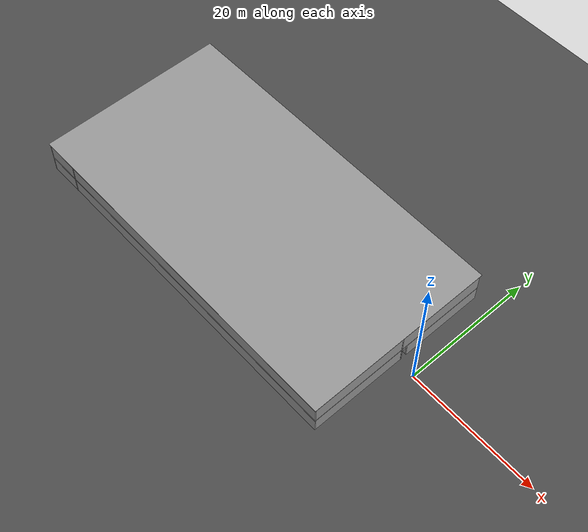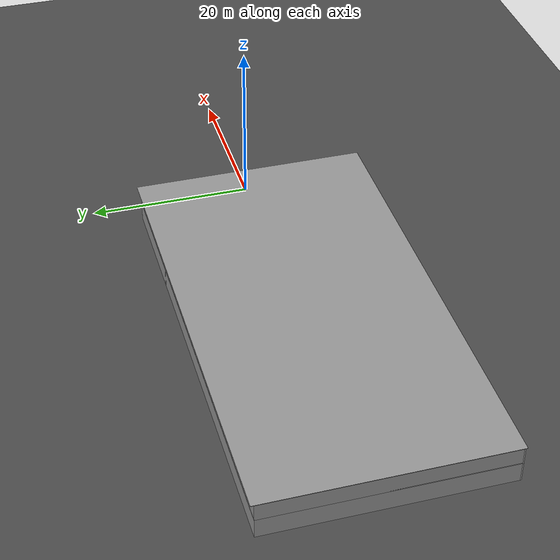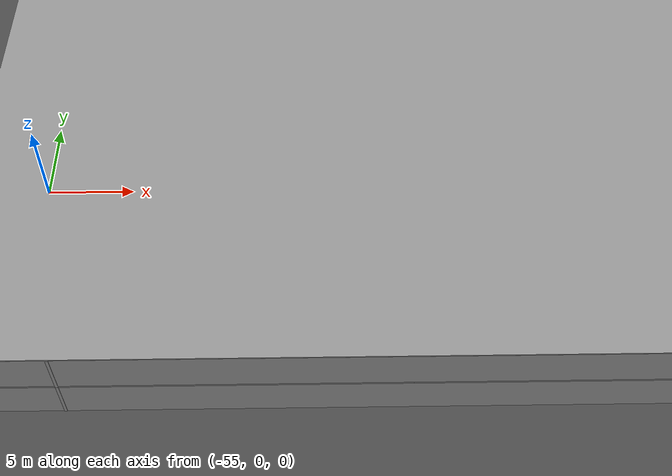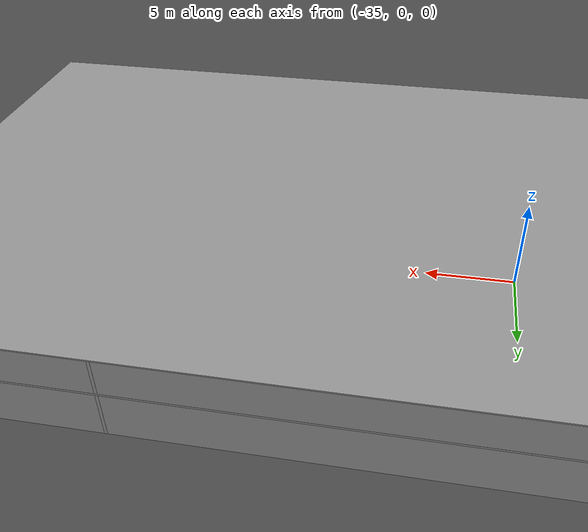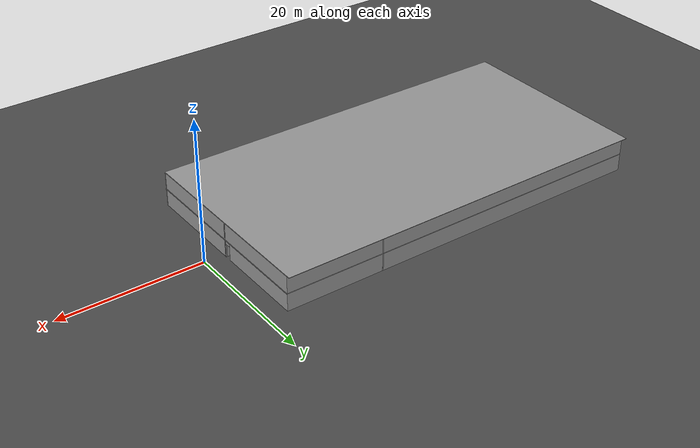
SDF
<sdf version="1.6">
 <world name="default">
  <light name="sun" type="directional">
   <pose>0 0 10 0 -0 0</pose>
   <diffuse>0.8 0.8 0.8 1</diffuse>
   <specular>0.2 0.2 0.2 1</specular>
   <attenuation>
    <range>1000</range>
    <constant>0.9</constant>
    <linear>0.01</linear>
    <quadratic>0.001</quadratic>
   </attenuation>
   <direction>-0.5 0.1 -0.9</direction>
  </light>
  <model name="ground_plane">
   <static>1</static>
   <link name="link">
    <collision name="collision">
     <geometry><plane><normal>0 0 1</normal><size>100 100</size></plane></geometry>
     <surface>
      <contact><collide_bitmask>65535</collide_bitmask></contact>
      <friction><ode><mu>100</mu><mu2>50</mu2></ode></friction>
     </surface>
    </collision>
    <visual name="visual">
     <cast_shadows>0</cast_shadows>
     <geometry><plane><normal>0 0 1</normal><size>100 100</size></plane></geometry>
     <material>
      <script><uri>file://media/materials/scripts/gazebo.material</uri><name>Gazebo/Grey</name></script>
     </material>
    </visual>
   </link>
  </model>
  <model name="asphalt_plane">
   <static>1</static>
   <link name="link">
    <collision name="collision"><geometry><box><size>200 200 0.1</size></box></geometry></collision>
    <visual name="visual">
     <cast_shadows>0</cast_shadows>
     <geometry><box><size>200 200 0.1</size></box></geometry>
     <material>
      <script>
       <uri>model://asphalt_plane/materials/scripts</uri>
       <uri>model://asphalt_plane/materials/textures</uri>
       <name>vrc/asphalt</name>
      </script>
     </material>
    </visual>
   </link>
  </model>
  <physics name="default_physics" default="0" type="ode">
   <ode>
    <solver>
     <type>quick</type>
     <iters>10</iters>
     <sor>1.3</sor>
     <use_dynamic_moi_rescaling>0</use_dynamic_moi_rescaling>
    </solver>
    <constraints>
     <cfm>0</cfm>
     <erp>0.2</erp>
     <contact_max_correcting_vel>100</contact_max_correcting_vel>
     <contact_surface_layer>0.001</contact_surface_layer>
    </constraints>
   </ode>
   <max_step_size>0.004</max_step_size>
   <real_time_factor>1</real_time_factor>
   <real_time_update_rate>250</real_time_update_rate>
  </physics>
  <gravity>0 0 -9.8066</gravity>
  <magnetic_field>6e-06 2.3e-05 -4.2e-05</magnetic_field>
  <atmosphere type="adiabatic"/>
  <scene><ambient>0.4 0.4 0.4 1</ambient><background>0.7 0.7 0.7 1</background><shadows>1</shadows></scene>
  <audio><device>default</device></audio>
  <spherical_coordinates>
   <surface_model>EARTH_WGS84</surface_model>
   <latitude_deg>0</latitude_deg>
   <longitude_deg>0</longitude_deg>
   <elevation>0</elevation>
   <heading_deg>0</heading_deg>
  </spherical_coordinates>
  <model name="Biggest">
   <link name="Floor_3">
    <pose>0 0 2.5 0 -0 0</pose>
    <visual name="Floor_3_Visual_1">
     <pose>11.2183 -12.6292 0.05 0 -0 0</pose>
     <geometry><box><size>32.1063 3.27346 0.1</size></box></geometry>
     <material>
      <script><uri>file://media/materials/scripts/gazebo.material</uri><name>Gazebo/Grey</name></script>
      <ambient>1 1 1 1</ambient>
     </material>
     <meta><layer>1</layer></meta>
    </visual>
    <visual name="Floor_3_Visual_3">
     <pose>-4.33484 3.38673 0.05 0 -0 0</pose>
     <geometry><box><size>1 21.7585 0.1</size></box></geometry>
     <material>
      <script><uri>file://media/materials/scripts/gazebo.material</uri><name>Gazebo/Grey</name></script>
      <ambient>1 1 1 1</ambient>
     </material>
     <meta><layer>1</layer></meta>
    </visual>
    <visual name="Floor_3_Visual_0">
     <pose>-16.0531 0 0.05 0 -0 0</pose>
     <geometry><box><size>22.4366 28.5319 0.1</size></box></geometry>
     <material>
      <script><uri>file://media/materials/scripts/gazebo.material</uri><name>Gazebo/Grey</name></script>
      <ambient>1 1 1 1</ambient>
     </material>
     <meta><layer>1</layer></meta>
    </visual>
    <visual name="Floor_3_Visual_2">
     <pose>11.7183 1.63673 0.05 0 -0 0</pose>
     <geometry><box><size>31.1063 25.2585 0.1</size></box></geometry>
     <material>
      <script><uri>file://media/materials/scripts/gazebo.material</uri><name>Gazebo/Grey</name></script>
      <ambient>1 1 1 1</ambient>
     </material>
     <meta><layer>1</layer></meta>
    </visual>
    <collision name="Floor_3_Collision_2">
     <pose>11.7183 1.63673 0.05 0 -0 0</pose>
     <geometry><box><size>31.1063 25.2585 0.1</size></box></geometry>
     <surface>
      <friction>
       <ode><mu>1</mu><mu2>1</mu2><fdir1>0 0 0</fdir1><slip1>0</slip1><slip2>0</slip2></ode>
       <torsional>
        <coefficient>1</coefficient>
        <patch_radius>0</patch_radius>
        <surface_radius>0</surface_radius>
        <use_patch_radius>1</use_patch_radius>
        <ode><slip>0</slip></ode>
       </torsional>
      </friction>
      <bounce><restitution_coefficient>0</restitution_coefficient><threshold>1e+06</threshold></bounce>
      <contact>
       <collide_without_contact>0</collide_without_contact>
       <collide_without_contact_bitmask>1</collide_without_contact_bitmask>
       <collide_bitmask>1</collide_bitmask>
       <ode>
        <soft_cfm>0</soft_cfm>
        <soft_erp>0.2</soft_erp>
        <kp>1e+13</kp>
        <kd>1</kd>
        <max_vel>0.01</max_vel>
        <min_depth>0</min_depth>
       </ode>
       <bullet>
        <split_impulse>1</split_impulse>
        <split_impulse_penetration_threshold>-0.01</split_impulse_penetration_threshold>
        <soft_cfm>0</soft_cfm>
        <soft_erp>0.2</soft_erp>
        <kp>1e+13</kp>
        <kd>1</kd>
       </bullet>
      </contact>
     </surface>
    </collision>
    <collision name="Floor_3_Collision_1">
     <pose>11.2183 -12.6292 0.05 0 -0 0</pose>
     <geometry><box><size>32.1063 3.27346 0.1</size></box></geometry>
     <surface>
      <friction>
       <ode><mu>1</mu><mu2>1</mu2><fdir1>0 0 0</fdir1><slip1>0</slip1><slip2>0</slip2></ode>
       <torsional>
        <coefficient>1</coefficient>
        <patch_radius>0</patch_radius>
        <surface_radius>0</surface_radius>
        <use_patch_radius>1</use_patch_radius>
        <ode><slip>0</slip></ode>
       </torsional>
      </friction>
      <bounce><restitution_coefficient>0</restitution_coefficient><threshold>1e+06</threshold></bounce>
      <contact>
       <collide_without_contact>0</collide_without_contact>
       <collide_without_contact_bitmask>1</collide_without_contact_bitmask>
       <collide_bitmask>1</collide_bitmask>
       <ode>
        <soft_cfm>0</soft_cfm>
        <soft_erp>0.2</soft_erp>
        <kp>1e+13</kp>
        <kd>1</kd>
        <max_vel>0.01</max_vel>
        <min_depth>0</min_depth>
       </ode>
       <bullet>
        <split_impulse>1</split_impulse>
        <split_impulse_penetration_threshold>-0.01</split_impulse_penetration_threshold>
        <soft_cfm>0</soft_cfm>
        <soft_erp>0.2</soft_erp>
        <kp>1e+13</kp>
        <kd>1</kd>
       </bullet>
      </contact>
     </surface>
    </collision>
    <collision name="Floor_3_Collision_3">
     <pose>-4.33484 3.38673 0.05 0 -0 0</pose>
     <geometry><box><size>1 21.7585 0.1</size></box></geometry>
     <surface>
      <friction>
       <ode><mu>1</mu><mu2>1</mu2><fdir1>0 0 0</fdir1><slip1>0</slip1><slip2>0</slip2></ode>
       <torsional>
        <coefficient>1</coefficient>
        <patch_radius>0</patch_radius>
        <surface_radius>0</surface_radius>
        <use_patch_radius>1</use_patch_radius>
        <ode><slip>0</slip></ode>
       </torsional>
      </friction>
      <bounce><restitution_coefficient>0</restitution_coefficient><threshold>1e+06</threshold></bounce>
      <contact>
       <collide_without_contact>0</collide_without_contact>
       <collide_without_contact_bitmask>1</collide_without_contact_bitmask>
       <collide_bitmask>1</collide_bitmask>
       <ode>
        <soft_cfm>0</soft_cfm>
        <soft_erp>0.2</soft_erp>
        <kp>1e+13</kp>
        <kd>1</kd>
        <max_vel>0.01</max_vel>
        <min_depth>0</min_depth>
       </ode>
       <bullet>
        <split_impulse>1</split_impulse>
        <split_impulse_penetration_threshold>-0.01</split_impulse_penetration_threshold>
        <soft_cfm>0</soft_cfm>
        <soft_erp>0.2</soft_erp>
        <kp>1e+13</kp>
        <kd>1</kd>
       </bullet>
      </contact>
     </surface>
    </collision>
    <collision name="Floor_3_Collision_0">
     <pose>-16.0531 0 0.05 0 -0 0</pose>
     <geometry><box><size>22.4366 28.5319 0.1</size></box></geometry>
     <surface>
      <friction>
       <ode><mu>1</mu><mu2>1</mu2><fdir1>0 0 0</fdir1><slip1>0</slip1><slip2>0</slip2></ode>
       <torsional>
        <coefficient>1</coefficient>
        <patch_radius>0</patch_radius>
        <surface_radius>0</surface_radius>
        <use_patch_radius>1</use_patch_radius>
        <ode><slip>0</slip></ode>
       </torsional>
      </friction>
      <bounce><restitution_coefficient>0</restitution_coefficient><threshold>1e+06</threshold></bounce>
      <contact>
       <collide_without_contact>0</collide_without_contact>
       <collide_without_contact_bitmask>1</collide_without_contact_bitmask>
       <collide_bitmask>1</collide_bitmask>
       <ode>
        <soft_cfm>0</soft_cfm>
        <soft_erp>0.2</soft_erp>
        <kp>1e+13</kp>
        <kd>1</kd>
        <max_vel>0.01</max_vel>
        <min_depth>0</min_depth>
       </ode>
       <bullet>
        <split_impulse>1</split_impulse>
        <split_impulse_penetration_threshold>-0.01</split_impulse_penetration_threshold>
        <soft_cfm>0</soft_cfm>
        <soft_erp>0.2</soft_erp>
        <kp>1e+13</kp>
        <kd>1</kd>
       </bullet>
      </contact>
     </surface>
    </collision>
   </link>
   <link name="Stairs_1">
    <visual name="Stairs_1_Visual_6">
     <pose>-4.33484 -9.00918 1.08333 0 -0 0</pose>
     <geometry><box><size>1 0.233333 0.166667</size></box></geometry>
     <material>
      <script><uri>file://media/materials/scripts/gazebo.material</uri><name>Gazebo/Grey</name></script>
      <ambient>1 1 1 1</ambient>
     </material>
     <meta><layer>0</layer></meta>
    </visual>
    <visual name="Stairs_1_Visual_2">
     <pose>-4.33484 -8.07584 0.416667 0 -0 0</pose>
     <geometry><box><size>1 0.233333 0.166667</size></box></geometry>
     <material>
      <script><uri>file://media/materials/scripts/gazebo.material</uri><name>Gazebo/Grey</name></script>
      <ambient>1 1 1 1</ambient>
     </material>
     <meta><layer>0</layer></meta>
    </visual>
    <visual name="Stairs_1_Visual_4">
     <pose>-4.33484 -8.54251 0.75 0 -0 0</pose>
     <geometry><box><size>1 0.233333 0.166667</size></box></geometry>
     <material>
      <script><uri>file://media/materials/scripts/gazebo.material</uri><name>Gazebo/Grey</name></script>
      <ambient>1 1 1 1</ambient>
     </material>
     <meta><layer>0</layer></meta>
    </visual>
    <visual name="Stairs_1_Visual_1">
     <pose>-4.33484 -7.84251 0.25 0 -0 0</pose>
     <geometry><box><size>1 0.233333 0.166667</size></box></geometry>
     <material>
      <script><uri>file://media/materials/scripts/gazebo.material</uri><name>Gazebo/Grey</name></script>
      <ambient>1 1 1 1</ambient>
     </material>
     <meta><layer>0</layer></meta>
    </visual>
    <visual name="Stairs_1_Visual_13">
     <pose>-4.33484 -10.6425 2.25 0 -0 0</pose>
     <geometry><box><size>1 0.233333 0.166667</size></box></geometry>
     <material>
      <script><uri>file://media/materials/scripts/gazebo.material</uri><name>Gazebo/Grey</name></script>
      <ambient>1 1 1 1</ambient>
     </material>
     <meta><layer>0</layer></meta>
    </visual>
    <visual name="Stairs_1_Visual_0">
     <pose>-4.33484 -7.60918 0.083333 0 -0 0</pose>
     <geometry><box><size>1 0.233333 0.166667</size></box></geometry>
     <material>
      <script><uri>file://media/materials/scripts/gazebo.material</uri><name>Gazebo/Grey</name></script>
      <ambient>1 1 1 1</ambient>
     </material>
     <meta><layer>0</layer></meta>
    </visual>
    <visual name="Stairs_1_Visual_9">
     <pose>-4.33484 -9.70918 1.58333 0 -0 0</pose>
     <geometry><box><size>1 0.233333 0.166667</size></box></geometry>
     <material>
      <script><uri>file://media/materials/scripts/gazebo.material</uri><name>Gazebo/Grey</name></script>
      <ambient>1 1 1 1</ambient>
     </material>
     <meta><layer>0</layer></meta>
    </visual>
    <visual name="Stairs_1_Visual_14">
     <pose>-4.33484 -10.8758 2.41667 0 -0 0</pose>
     <geometry><box><size>1 0.233333 0.166667</size></box></geometry>
     <material>
      <script><uri>file://media/materials/scripts/gazebo.material</uri><name>Gazebo/Grey</name></script>
      <ambient>1 1 1 1</ambient>
     </material>
     <meta><layer>0</layer></meta>
    </visual>
    <visual name="Stairs_1_Visual_3">
     <pose>-4.33484 -8.30917 0.583333 0 -0 0</pose>
     <geometry><box><size>1 0.233333 0.166667</size></box></geometry>
     <material>
      <script><uri>file://media/materials/scripts/gazebo.material</uri><name>Gazebo/Grey</name></script>
      <ambient>1 1 1 1</ambient>
     </material>
     <meta><layer>0</layer></meta>
    </visual>
    <visual name="Stairs_1_Visual_5">
     <pose>-4.33484 -8.77584 0.916667 0 -0 0</pose>
     <geometry><box><size>1 0.233333 0.166667</size></box></geometry>
     <material>
      <script><uri>file://media/materials/scripts/gazebo.material</uri><name>Gazebo/Grey</name></script>
      <ambient>1 1 1 1</ambient>
     </material>
     <meta><layer>0</layer></meta>
    </visual>
    <visual name="Stairs_1_Visual_10">
     <pose>-4.33484 -9.94251 1.75 0 -0 0</pose>
     <geometry><box><size>1 0.233333 0.166667</size></box></geometry>
     <material>
      <script><uri>file://media/materials/scripts/gazebo.material</uri><name>Gazebo/Grey</name></script>
      <ambient>1 1 1 1</ambient>
     </material>
     <meta><layer>0</layer></meta>
    </visual>
    <visual name="Stairs_1_Visual_8">
     <pose>-4.33484 -9.47584 1.41667 0 -0 0</pose>
     <geometry><box><size>1 0.233333 0.166667</size></box></geometry>
     <material>
      <script><uri>file://media/materials/scripts/gazebo.material</uri><name>Gazebo/Grey</name></script>
      <ambient>1 1 1 1</ambient>
     </material>
     <meta><layer>0</layer></meta>
    </visual>
    <visual name="Stairs_1_Visual_11">
     <pose>-4.33484 -10.1758 1.91667 0 -0 0</pose>
     <geometry><box><size>1 0.233333 0.166667</size></box></geometry>
     <material>
      <script><uri>file://media/materials/scripts/gazebo.material</uri><name>Gazebo/Grey</name></script>
      <ambient>1 1 1 1</ambient>
     </material>
     <meta><layer>0</layer></meta>
    </visual>
    <visual name="Stairs_1_Visual_7">
     <pose>-4.33484 -9.24251 1.25 0 -0 0</pose>
     <geometry><box><size>1 0.233333 0.166667</size></box></geometry>
     <material>
      <script><uri>file://media/materials/scripts/gazebo.material</uri><name>Gazebo/Grey</name></script>
      <ambient>1 1 1 1</ambient>
     </material>
     <meta><layer>0</layer></meta>
    </visual>
    <visual name="Stairs_1_Visual_12">
     <pose>-4.33484 -10.4092 2.08333 0 -0 0</pose>
     <geometry><box><size>1 0.233333 0.166667</size></box></geometry>
     <material>
      <script><uri>file://media/materials/scripts/gazebo.material</uri><name>Gazebo/Grey</name></script>
      <ambient>1 1 1 1</ambient>
     </material>
     <meta><layer>0</layer></meta>
    </visual>
    <collision name="Stairs_1_Collision_6">
     <pose>-4.33484 -9.00918 1.08333 0 -0 0</pose>
     <geometry><box><size>1 0.233333 0.166667</size></box></geometry>
     <surface>
      <friction>
       <ode><mu>1</mu><mu2>1</mu2><fdir1>0 0 0</fdir1><slip1>0</slip1><slip2>0</slip2></ode>
       <torsional>
        <coefficient>1</coefficient>
        <patch_radius>0</patch_radius>
        <surface_radius>0</surface_radius>
        <use_patch_radius>1</use_patch_radius>
        <ode><slip>0</slip></ode>
       </torsional>
      </friction>
      <bounce><restitution_coefficient>0</restitution_coefficient><threshold>1e+06</threshold></bounce>
      <contact>
       <collide_without_contact>0</collide_without_contact>
       <collide_without_contact_bitmask>1</collide_without_contact_bitmask>
       <collide_bitmask>1</collide_bitmask>
       <ode>
        <soft_cfm>0</soft_cfm>
        <soft_erp>0.2</soft_erp>
        <kp>1e+13</kp>
        <kd>1</kd>
        <max_vel>0.01</max_vel>
        <min_depth>0</min_depth>
       </ode>
       <bullet>
        <split_impulse>1</split_impulse>
        <split_impulse_penetration_threshold>-0.01</split_impulse_penetration_threshold>
        <soft_cfm>0</soft_cfm>
        <soft_erp>0.2</soft_erp>
        <kp>1e+13</kp>
        <kd>1</kd>
       </bullet>
      </contact>
     </surface>
    </collision>
    <collision name="Stairs_1_Collision_5">
     <pose>-4.33484 -8.77584 0.916667 0 -0 0</pose>
     <geometry><box><size>1 0.233333 0.166667</size></box></geometry>
     <surface>
      <friction>
       <ode><mu>1</mu><mu2>1</mu2><fdir1>0 0 0</fdir1><slip1>0</slip1><slip2>0</slip2></ode>
       <torsional>
        <coefficient>1</coefficient>
        <patch_radius>0</patch_radius>
        <surface_radius>0</surface_radius>
        <use_patch_radius>1</use_patch_radius>
        <ode><slip>0</slip></ode>
       </torsional>
      </friction>
      <bounce><restitution_coefficient>0</restitution_coefficient><threshold>1e+06</threshold></bounce>
      <contact>
       <collide_without_contact>0</collide_without_contact>
       <collide_without_contact_bitmask>1</collide_without_contact_bitmask>
       <collide_bitmask>1</collide_bitmask>
       <ode>
        <soft_cfm>0</soft_cfm>
        <soft_erp>0.2</soft_erp>
        <kp>1e+13</kp>
        <kd>1</kd>
        <max_vel>0.01</max_vel>
        <min_depth>0</min_depth>
       </ode>
       <bullet>
        <split_impulse>1</split_impulse>
        <split_impulse_penetration_threshold>-0.01</split_impulse_penetration_threshold>
        <soft_cfm>0</soft_cfm>
        <soft_erp>0.2</soft_erp>
        <kp>1e+13</kp>
        <kd>1</kd>
       </bullet>
      </contact>
     </surface>
    </collision>
    <collision name="Stairs_1_Collision_1">
     <pose>-4.33484 -7.84251 0.25 0 -0 0</pose>
     <geometry><box><size>1 0.233333 0.166667</size></box></geometry>
     <surface>
      <friction>
       <ode><mu>1</mu><mu2>1</mu2><fdir1>0 0 0</fdir1><slip1>0</slip1><slip2>0</slip2></ode>
       <torsional>
        <coefficient>1</coefficient>
        <patch_radius>0</patch_radius>
        <surface_radius>0</surface_radius>
        <use_patch_radius>1</use_patch_radius>
        <ode><slip>0</slip></ode>
       </torsional>
      </friction>
      <bounce><restitution_coefficient>0</restitution_coefficient><threshold>1e+06</threshold></bounce>
      <contact>
       <collide_without_contact>0</collide_without_contact>
       <collide_without_contact_bitmask>1</collide_without_contact_bitmask>
       <collide_bitmask>1</collide_bitmask>
       <ode>
        <soft_cfm>0</soft_cfm>
        <soft_erp>0.2</soft_erp>
        <kp>1e+13</kp>
        <kd>1</kd>
        <max_vel>0.01</max_vel>
        <min_depth>0</min_depth>
       </ode>
       <bullet>
        <split_impulse>1</split_impulse>
        <split_impulse_penetration_threshold>-0.01</split_impulse_penetration_threshold>
        <soft_cfm>0</soft_cfm>
        <soft_erp>0.2</soft_erp>
        <kp>1e+13</kp>
        <kd>1</kd>
       </bullet>
      </contact>
     </surface>
    </collision>
    <collision name="Stairs_1_Collision_9">
     <pose>-4.33484 -9.70918 1.58333 0 -0 0</pose>
     <geometry><box><size>1 0.233333 0.166667</size></box></geometry>
     <surface>
      <friction>
       <ode><mu>1</mu><mu2>1</mu2><fdir1>0 0 0</fdir1><slip1>0</slip1><slip2>0</slip2></ode>
       <torsional>
        <coefficient>1</coefficient>
        <patch_radius>0</patch_radius>
        <surface_radius>0</surface_radius>
        <use_patch_radius>1</use_patch_radius>
        <ode><slip>0</slip></ode>
       </torsional>
      </friction>
      <bounce><restitution_coefficient>0</restitution_coefficient><threshold>1e+06</threshold></bounce>
      <contact>
       <collide_without_contact>0</collide_without_contact>
       <collide_without_contact_bitmask>1</collide_without_contact_bitmask>
       <collide_bitmask>1</collide_bitmask>
       <ode>
        <soft_cfm>0</soft_cfm>
        <soft_erp>0.2</soft_erp>
        <kp>1e+13</kp>
        <kd>1</kd>
        <max_vel>0.01</max_vel>
        <min_depth>0</min_depth>
       </ode>
       <bullet>
        <split_impulse>1</split_impulse>
        <split_impulse_penetration_threshold>-0.01</split_impulse_penetration_threshold>
        <soft_cfm>0</soft_cfm>
        <soft_erp>0.2</soft_erp>
        <kp>1e+13</kp>
        <kd>1</kd>
       </bullet>
      </contact>
     </surface>
    </collision>
    <collision name="Stairs_1_Collision_12">
     <pose>-4.33484 -10.4092 2.08333 0 -0 0</pose>
     <geometry><box><size>1 0.233333 0.166667</size></box></geometry>
     <surface>
      <friction>
       <ode><mu>1</mu><mu2>1</mu2><fdir1>0 0 0</fdir1><slip1>0</slip1><slip2>0</slip2></ode>
       <torsional>
        <coefficient>1</coefficient>
        <patch_radius>0</patch_radius>
        <surface_radius>0</surface_radius>
        <use_patch_radius>1</use_patch_radius>
        <ode><slip>0</slip></ode>
       </torsional>
      </friction>
      <bounce><restitution_coefficient>0</restitution_coefficient><threshold>1e+06</threshold></bounce>
      <contact>
       <collide_without_contact>0</collide_without_contact>
       <collide_without_contact_bitmask>1</collide_without_contact_bitmask>
       <collide_bitmask>1</collide_bitmask>
       <ode>
        <soft_cfm>0</soft_cfm>
        <soft_erp>0.2</soft_erp>
        <kp>1e+13</kp>
        <kd>1</kd>
        <max_vel>0.01</max_vel>
        <min_depth>0</min_depth>
       </ode>
       <bullet>
        <split_impulse>1</split_impulse>
        <split_impulse_penetration_threshold>-0.01</split_impulse_penetration_threshold>
        <soft_cfm>0</soft_cfm>
        <soft_erp>0.2</soft_erp>
        <kp>1e+13</kp>
        <kd>1</kd>
       </bullet>
      </contact>
     </surface>
    </collision>
    <collision name="Stairs_1_Collision_2">
     <pose>-4.33484 -8.07584 0.416667 0 -0 0</pose>
     <geometry><box><size>1 0.233333 0.166667</size></box></geometry>
     <surface>
      <friction>
       <ode><mu>1</mu><mu2>1</mu2><fdir1>0 0 0</fdir1><slip1>0</slip1><slip2>0</slip2></ode>
       <torsional>
        <coefficient>1</coefficient>
        <patch_radius>0</patch_radius>
        <surface_radius>0</surface_radius>
        <use_patch_radius>1</use_patch_radius>
        <ode><slip>0</slip></ode>
       </torsional>
      </friction>
      <bounce><restitution_coefficient>0</restitution_coefficient><threshold>1e+06</threshold></bounce>
      <contact>
       <collide_without_contact>0</collide_without_contact>
       <collide_without_contact_bitmask>1</collide_without_contact_bitmask>
       <collide_bitmask>1</collide_bitmask>
       <ode>
        <soft_cfm>0</soft_cfm>
        <soft_erp>0.2</soft_erp>
        <kp>1e+13</kp>
        <kd>1</kd>
        <max_vel>0.01</max_vel>
        <min_depth>0</min_depth>
       </ode>
       <bullet>
        <split_impulse>1</split_impulse>
        <split_impulse_penetration_threshold>-0.01</split_impulse_penetration_threshold>
        <soft_cfm>0</soft_cfm>
        <soft_erp>0.2</soft_erp>
        <kp>1e+13</kp>
        <kd>1</kd>
       </bullet>
      </contact>
     </surface>
    </collision>
    <collision name="Stairs_1_Collision_10">
     <pose>-4.33484 -9.94251 1.75 0 -0 0</pose>
     <geometry><box><size>1 0.233333 0.166667</size></box></geometry>
     <surface>
      <friction>
       <ode><mu>1</mu><mu2>1</mu2><fdir1>0 0 0</fdir1><slip1>0</slip1><slip2>0</slip2></ode>
       <torsional>
        <coefficient>1</coefficient>
        <patch_radius>0</patch_radius>
        <surface_radius>0</surface_radius>
        <use_patch_radius>1</use_patch_radius>
        <ode><slip>0</slip></ode>
       </torsional>
      </friction>
      <bounce><restitution_coefficient>0</restitution_coefficient><threshold>1e+06</threshold></bounce>
      <contact>
       <collide_without_contact>0</collide_without_contact>
       <collide_without_contact_bitmask>1</collide_without_contact_bitmask>
       <collide_bitmask>1</collide_bitmask>
       <ode>
        <soft_cfm>0</soft_cfm>
        <soft_erp>0.2</soft_erp>
        <kp>1e+13</kp>
        <kd>1</kd>
        <max_vel>0.01</max_vel>
        <min_depth>0</min_depth>
       </ode>
       <bullet>
        <split_impulse>1</split_impulse>
        <split_impulse_penetration_threshold>-0.01</split_impulse_penetration_threshold>
        <soft_cfm>0</soft_cfm>
        <soft_erp>0.2</soft_erp>
        <kp>1e+13</kp>
        <kd>1</kd>
       </bullet>
      </contact>
     </surface>
    </collision>
    <collision name="Stairs_1_Collision_3">
     <pose>-4.33484 -8.30917 0.583333 0 -0 0</pose>
     <geometry><box><size>1 0.233333 0.166667</size></box></geometry>
     <surface>
      <friction>
       <ode><mu>1</mu><mu2>1</mu2><fdir1>0 0 0</fdir1><slip1>0</slip1><slip2>0</slip2></ode>
       <torsional>
        <coefficient>1</coefficient>
        <patch_radius>0</patch_radius>
        <surface_radius>0</surface_radius>
        <use_patch_radius>1</use_patch_radius>
        <ode><slip>0</slip></ode>
       </torsional>
      </friction>
      <bounce><restitution_coefficient>0</restitution_coefficient><threshold>1e+06</threshold></bounce>
      <contact>
       <collide_without_contact>0</collide_without_contact>
       <collide_without_contact_bitmask>1</collide_without_contact_bitmask>
       <collide_bitmask>1</collide_bitmask>
       <ode>
        <soft_cfm>0</soft_cfm>
        <soft_erp>0.2</soft_erp>
        <kp>1e+13</kp>
        <kd>1</kd>
        <max_vel>0.01</max_vel>
        <min_depth>0</min_depth>
       </ode>
       <bullet>
        <split_impulse>1</split_impulse>
        <split_impulse_penetration_threshold>-0.01</split_impulse_penetration_threshold>
        <soft_cfm>0</soft_cfm>
        <soft_erp>0.2</soft_erp>
        <kp>1e+13</kp>
        <kd>1</kd>
       </bullet>
      </contact>
     </surface>
    </collision>
    <collision name="Stairs_1_Collision_7">
     <pose>-4.33484 -9.24251 1.25 0 -0 0</pose>
     <geometry><box><size>1 0.233333 0.166667</size></box></geometry>
     <surface>
      <friction>
       <ode><mu>1</mu><mu2>1</mu2><fdir1>0 0 0</fdir1><slip1>0</slip1><slip2>0</slip2></ode>
       <torsional>
        <coefficient>1</coefficient>
        <patch_radius>0</patch_radius>
        <surface_radius>0</surface_radius>
        <use_patch_radius>1</use_patch_radius>
        <ode><slip>0</slip></ode>
       </torsional>
      </friction>
      <bounce><restitution_coefficient>0</restitution_coefficient><threshold>1e+06</threshold></bounce>
      <contact>
       <collide_without_contact>0</collide_without_contact>
       <collide_without_contact_bitmask>1</collide_without_contact_bitmask>
       <collide_bitmask>1</collide_bitmask>
       <ode>
        <soft_cfm>0</soft_cfm>
        <soft_erp>0.2</soft_erp>
        <kp>1e+13</kp>
        <kd>1</kd>
        <max_vel>0.01</max_vel>
        <min_depth>0</min_depth>
       </ode>
       <bullet>
        <split_impulse>1</split_impulse>
        <split_impulse_penetration_threshold>-0.01</split_impulse_penetration_threshold>
        <soft_cfm>0</soft_cfm>
        <soft_erp>0.2</soft_erp>
        <kp>1e+13</kp>
        <kd>1</kd>
       </bullet>
      </contact>
     </surface>
    </collision>
    <collision name="Stairs_1_Collision_0">
     <pose>-4.33484 -7.60918 0.083333 0 -0 0</pose>
     <geometry><box><size>1 0.233333 0.166667</size></box></geometry>
     <surface>
      <friction>
       <ode><mu>1</mu><mu2>1</mu2><fdir1>0 0 0</fdir1><slip1>0</slip1><slip2>0</slip2></ode>
       <torsional>
        <coefficient>1</coefficient>
        <patch_radius>0</patch_radius>
        <surface_radius>0</surface_radius>
        <use_patch_radius>1</use_patch_radius>
        <ode><slip>0</slip></ode>
       </torsional>
      </friction>
      <bounce><restitution_coefficient>0</restitution_coefficient><threshold>1e+06</threshold></bounce>
      <contact>
       <collide_without_contact>0</collide_without_contact>
       <collide_without_contact_bitmask>1</collide_without_contact_bitmask>
       <collide_bitmask>1</collide_bitmask>
       <ode>
        <soft_cfm>0</soft_cfm>
        <soft_erp>0.2</soft_erp>
        <kp>1e+13</kp>
        <kd>1</kd>
        <max_vel>0.01</max_vel>
        <min_depth>0</min_depth>
       </ode>
       <bullet>
        <split_impulse>1</split_impulse>
        <split_impulse_penetration_threshold>-0.01</split_impulse_penetration_threshold>
        <soft_cfm>0</soft_cfm>
        <soft_erp>0.2</soft_erp>
        <kp>1e+13</kp>
        <kd>1</kd>
       </bullet>
      </contact>
     </surface>
    </collision>
    <collision name="Stairs_1_Collision_14">
     <pose>-4.33484 -10.8758 2.41667 0 -0 0</pose>
     <geometry><box><size>1 0.233333 0.166667</size></box></geometry>
     <surface>
      <friction>
       <ode><mu>1</mu><mu2>1</mu2><fdir1>0 0 0</fdir1><slip1>0</slip1><slip2>0</slip2></ode>
       <torsional>
        <coefficient>1</coefficient>
        <patch_radius>0</patch_radius>
        <surface_radius>0</surface_radius>
        <use_patch_radius>1</use_patch_radius>
        <ode><slip>0</slip></ode>
       </torsional>
      </friction>
      <bounce><restitution_coefficient>0</restitution_coefficient><threshold>1e+06</threshold></bounce>
      <contact>
       <collide_without_contact>0</collide_without_contact>
       <collide_without_contact_bitmask>1</collide_without_contact_bitmask>
       <collide_bitmask>1</collide_bitmask>
       <ode>
        <soft_cfm>0</soft_cfm>
        <soft_erp>0.2</soft_erp>
        <kp>1e+13</kp>
        <kd>1</kd>
        <max_vel>0.01</max_vel>
        <min_depth>0</min_depth>
       </ode>
       <bullet>
        <split_impulse>1</split_impulse>
        <split_impulse_penetration_threshold>-0.01</split_impulse_penetration_threshold>
        <soft_cfm>0</soft_cfm>
        <soft_erp>0.2</soft_erp>
        <kp>1e+13</kp>
        <kd>1</kd>
       </bullet>
      </contact>
     </surface>
    </collision>
    <collision name="Stairs_1_Collision_8">
     <pose>-4.33484 -9.47584 1.41667 0 -0 0</pose>
     <geometry><box><size>1 0.233333 0.166667</size></box></geometry>
     <surface>
      <friction>
       <ode><mu>1</mu><mu2>1</mu2><fdir1>0 0 0</fdir1><slip1>0</slip1><slip2>0</slip2></ode>
       <torsional>
        <coefficient>1</coefficient>
        <patch_radius>0</patch_radius>
        <surface_radius>0</surface_radius>
        <use_patch_radius>1</use_patch_radius>
        <ode><slip>0</slip></ode>
       </torsional>
      </friction>
      <bounce><restitution_coefficient>0</restitution_coefficient><threshold>1e+06</threshold></bounce>
      <contact>
       <collide_without_contact>0</collide_without_contact>
       <collide_without_contact_bitmask>1</collide_without_contact_bitmask>
       <collide_bitmask>1</collide_bitmask>
       <ode>
        <soft_cfm>0</soft_cfm>
        <soft_erp>0.2</soft_erp>
        <kp>1e+13</kp>
        <kd>1</kd>
        <max_vel>0.01</max_vel>
        <min_depth>0</min_depth>
       </ode>
       <bullet>
        <split_impulse>1</split_impulse>
        <split_impulse_penetration_threshold>-0.01</split_impulse_penetration_threshold>
        <soft_cfm>0</soft_cfm>
        <soft_erp>0.2</soft_erp>
        <kp>1e+13</kp>
        <kd>1</kd>
       </bullet>
      </contact>
     </surface>
    </collision>
    <collision name="Stairs_1_Collision_13">
     <pose>-4.33484 -10.6425 2.25 0 -0 0</pose>
     <geometry><box><size>1 0.233333 0.166667</size></box></geometry>
     <surface>
      <friction>
       <ode><mu>1</mu><mu2>1</mu2><fdir1>0 0 0</fdir1><slip1>0</slip1><slip2>0</slip2></ode>
       <torsional>
        <coefficient>1</coefficient>
        <patch_radius>0</patch_radius>
        <surface_radius>0</surface_radius>
        <use_patch_radius>1</use_patch_radius>
        <ode><slip>0</slip></ode>
       </torsional>
      </friction>
      <bounce><restitution_coefficient>0</restitution_coefficient><threshold>1e+06</threshold></bounce>
      <contact>
       <collide_without_contact>0</collide_without_contact>
       <collide_without_contact_bitmask>1</collide_without_contact_bitmask>
       <collide_bitmask>1</collide_bitmask>
       <ode>
        <soft_cfm>0</soft_cfm>
        <soft_erp>0.2</soft_erp>
        <kp>1e+13</kp>
        <kd>1</kd>
        <max_vel>0.01</max_vel>
        <min_depth>0</min_depth>
       </ode>
       <bullet>
        <split_impulse>1</split_impulse>
        <split_impulse_penetration_threshold>-0.01</split_impulse_penetration_threshold>
        <soft_cfm>0</soft_cfm>
        <soft_erp>0.2</soft_erp>
        <kp>1e+13</kp>
        <kd>1</kd>
       </bullet>
      </contact>
     </surface>
    </collision>
    <collision name="Stairs_1_Collision_11">
     <pose>-4.33484 -10.1758 1.91667 0 -0 0</pose>
     <geometry><box><size>1 0.233333 0.166667</size></box></geometry>
     <surface>
      <friction>
       <ode><mu>1</mu><mu2>1</mu2><fdir1>0 0 0</fdir1><slip1>0</slip1><slip2>0</slip2></ode>
       <torsional>
        <coefficient>1</coefficient>
        <patch_radius>0</patch_radius>
        <surface_radius>0</surface_radius>
        <use_patch_radius>1</use_patch_radius>
        <ode><slip>0</slip></ode>
       </torsional>
      </friction>
      <bounce><restitution_coefficient>0</restitution_coefficient><threshold>1e+06</threshold></bounce>
      <contact>
       <collide_without_contact>0</collide_without_contact>
       <collide_without_contact_bitmask>1</collide_without_contact_bitmask>
       <collide_bitmask>1</collide_bitmask>
       <ode>
        <soft_cfm>0</soft_cfm>
        <soft_erp>0.2</soft_erp>
        <kp>1e+13</kp>
        <kd>1</kd>
        <max_vel>0.01</max_vel>
        <min_depth>0</min_depth>
       </ode>
       <bullet>
        <split_impulse>1</split_impulse>
        <split_impulse_penetration_threshold>-0.01</split_impulse_penetration_threshold>
        <soft_cfm>0</soft_cfm>
        <soft_erp>0.2</soft_erp>
        <kp>1e+13</kp>
        <kd>1</kd>
       </bullet>
      </contact>
     </surface>
    </collision>
    <collision name="Stairs_1_Collision_4">
     <pose>-4.33484 -8.54251 0.75 0 -0 0</pose>
     <geometry><box><size>1 0.233333 0.166667</size></box></geometry>
     <surface>
      <friction>
       <ode><mu>1</mu><mu2>1</mu2><fdir1>0 0 0</fdir1><slip1>0</slip1><slip2>0</slip2></ode>
       <torsional>
        <coefficient>1</coefficient>
        <patch_radius>0</patch_radius>
        <surface_radius>0</surface_radius>
        <use_patch_radius>1</use_patch_radius>
        <ode><slip>0</slip></ode>
       </torsional>
      </friction>
      <bounce><restitution_coefficient>0</restitution_coefficient><threshold>1e+06</threshold></bounce>
      <contact>
       <collide_without_contact>0</collide_without_contact>
       <collide_without_contact_bitmask>1</collide_without_contact_bitmask>
       <collide_bitmask>1</collide_bitmask>
       <ode>
        <soft_cfm>0</soft_cfm>
        <soft_erp>0.2</soft_erp>
        <kp>1e+13</kp>
        <kd>1</kd>
        <max_vel>0.01</max_vel>
        <min_depth>0</min_depth>
       </ode>
       <bullet>
        <split_impulse>1</split_impulse>
        <split_impulse_penetration_threshold>-0.01</split_impulse_penetration_threshold>
        <soft_cfm>0</soft_cfm>
        <soft_erp>0.2</soft_erp>
        <kp>1e+13</kp>
        <kd>1</kd>
       </bullet>
      </contact>
     </surface>
    </collision>
   </link>
   <link name="Wall_101">
    <pose>-20.1199 -7.02638 0 0 0 -3.12807</pose>
    <visual name="Wall_101_Visual">
     <pose>0 0 1.25 0 -0 0</pose>
     <geometry><box><size>3.63056 0.15 2.5</size></box></geometry>
     <material>
      <script><uri>file://media/materials/scripts/gazebo.material</uri><name>Gazebo/Grey</name></script>
      <ambient>1 1 1 1</ambient>
     </material>
     <meta><layer>0</layer></meta>
    </visual>
    <collision name="Wall_101_Collision">
     <pose>0 0 1.25 0 -0 0</pose>
     <geometry><box><size>3.63056 0.15 2.5</size></box></geometry>
     <surface>
      <friction>
       <ode><mu>1</mu><mu2>1</mu2><fdir1>0 0 0</fdir1><slip1>0</slip1><slip2>0</slip2></ode>
       <torsional>
        <coefficient>1</coefficient>
        <patch_radius>0</patch_radius>
        <surface_radius>0</surface_radius>
        <use_patch_radius>1</use_patch_radius>
        <ode><slip>0</slip></ode>
       </torsional>
      </friction>
      <bounce><restitution_coefficient>0</restitution_coefficient><threshold>1e+06</threshold></bounce>
      <contact>
       <collide_without_contact>0</collide_without_contact>
       <collide_without_contact_bitmask>1</collide_without_contact_bitmask>
       <collide_bitmask>1</collide_bitmask>
       <ode>
        <soft_cfm>0</soft_cfm>
        <soft_erp>0.2</soft_erp>
        <kp>1e+13</kp>
        <kd>1</kd>
        <max_vel>0.01</max_vel>
        <min_depth>0</min_depth>
       </ode>
       <bullet>
        <split_impulse>1</split_impulse>
        <split_impulse_penetration_threshold>-0.01</split_impulse_penetration_threshold>
        <soft_cfm>0</soft_cfm>
        <soft_erp>0.2</soft_erp>
        <kp>1e+13</kp>
        <kd>1</kd>
       </bullet>
      </contact>
     </surface>
    </collision>
   </link>
   <link name="Wall_103">
    <pose>-9.33292 -5.35177 0 0 0 -1.5708</pose>
    <visual name="Wall_103_Visual">
     <pose>0 0 1.25 0 -0 0</pose>
     <geometry><box><size>11.75 0.15 2.5</size></box></geometry>
     <material>
      <script><uri>file://media/materials/scripts/gazebo.material</uri><name>Gazebo/Grey</name></script>
      <ambient>1 1 1 1</ambient>
     </material>
     <meta><layer>0</layer></meta>
    </visual>
    <collision name="Wall_103_Collision">
     <pose>0 0 1.25 0 -0 0</pose>
     <geometry><box><size>11.75 0.15 2.5</size></box></geometry>
     <surface>
      <friction>
       <ode><mu>1</mu><mu2>1</mu2><fdir1>0 0 0</fdir1><slip1>0</slip1><slip2>0</slip2></ode>
       <torsional>
        <coefficient>1</coefficient>
        <patch_radius>0</patch_radius>
        <surface_radius>0</surface_radius>
        <use_patch_radius>1</use_patch_radius>
        <ode><slip>0</slip></ode>
       </torsional>
      </friction>
      <bounce><restitution_coefficient>0</restitution_coefficient><threshold>1e+06</threshold></bounce>
      <contact>
       <collide_without_contact>0</collide_without_contact>
       <collide_without_contact_bitmask>1</collide_without_contact_bitmask>
       <collide_bitmask>1</collide_bitmask>
       <ode>
        <soft_cfm>0</soft_cfm>
        <soft_erp>0.2</soft_erp>
        <kp>1e+13</kp>
        <kd>1</kd>
        <max_vel>0.01</max_vel>
        <min_depth>0</min_depth>
       </ode>
       <bullet>
        <split_impulse>1</split_impulse>
        <split_impulse_penetration_threshold>-0.01</split_impulse_penetration_threshold>
        <soft_cfm>0</soft_cfm>
        <soft_erp>0.2</soft_erp>
        <kp>1e+13</kp>
        <kd>1</kd>
       </bullet>
      </contact>
     </surface>
    </collision>
   </link>
   <link name="Wall_104">
    <pose>8.84208 -11.1518 0 0 -0 0</pose>
    <visual name="Wall_104_Visual">
     <pose>0 0 1.25 0 -0 0</pose>
     <geometry><box><size>36.5 0.15 2.5</size></box></geometry>
     <material>
      <script><uri>file://media/materials/scripts/gazebo.material</uri><name>Gazebo/Grey</name></script>
      <ambient>1 1 1 1</ambient>
     </material>
     <meta><layer>0</layer></meta>
    </visual>
    <collision name="Wall_104_Collision">
     <pose>0 0 1.25 0 -0 0</pose>
     <geometry><box><size>36.5 0.15 2.5</size></box></geometry>
     <surface>
      <friction>
       <ode><mu>1</mu><mu2>1</mu2><fdir1>0 0 0</fdir1><slip1>0</slip1><slip2>0</slip2></ode>
       <torsional>
        <coefficient>1</coefficient>
        <patch_radius>0</patch_radius>
        <surface_radius>0</surface_radius>
        <use_patch_radius>1</use_patch_radius>
        <ode><slip>0</slip></ode>
       </torsional>
      </friction>
      <bounce><restitution_coefficient>0</restitution_coefficient><threshold>1e+06</threshold></bounce>
      <contact>
       <collide_without_contact>0</collide_without_contact>
       <collide_without_contact_bitmask>1</collide_without_contact_bitmask>
       <collide_bitmask>1</collide_bitmask>
       <ode>
        <soft_cfm>0</soft_cfm>
        <soft_erp>0.2</soft_erp>
        <kp>1e+13</kp>
        <kd>1</kd>
        <max_vel>0.01</max_vel>
        <min_depth>0</min_depth>
       </ode>
       <bullet>
        <split_impulse>1</split_impulse>
        <split_impulse_penetration_threshold>-0.01</split_impulse_penetration_threshold>
        <soft_cfm>0</soft_cfm>
        <soft_erp>0.2</soft_erp>
        <kp>1e+13</kp>
        <kd>1</kd>
       </bullet>
      </contact>
     </surface>
    </collision>
   </link>
   <link name="Wall_106">
    <pose>-3.73234 -5.28954 0 0 0 -1.5708</pose>
    <visual name="Wall_106_Visual">
     <pose>0 0 1.25 0 -0 0</pose>
     <geometry><box><size>11.75 0.15 2.5</size></box></geometry>
     <material>
      <script><uri>file://media/materials/scripts/gazebo.material</uri><name>Gazebo/Grey</name></script>
      <ambient>1 1 1 1</ambient>
     </material>
     <meta><layer>0</layer></meta>
    </visual>
    <collision name="Wall_106_Collision">
     <pose>0 0 1.25 0 -0 0</pose>
     <geometry><box><size>11.75 0.15 2.5</size></box></geometry>
     <surface>
      <friction>
       <ode><mu>1</mu><mu2>1</mu2><fdir1>0 0 0</fdir1><slip1>0</slip1><slip2>0</slip2></ode>
       <torsional>
        <coefficient>1</coefficient>
        <patch_radius>0</patch_radius>
        <surface_radius>0</surface_radius>
        <use_patch_radius>1</use_patch_radius>
        <ode><slip>0</slip></ode>
       </torsional>
      </friction>
      <bounce><restitution_coefficient>0</restitution_coefficient><threshold>1e+06</threshold></bounce>
      <contact>
       <collide_without_contact>0</collide_without_contact>
       <collide_without_contact_bitmask>1</collide_without_contact_bitmask>
       <collide_bitmask>1</collide_bitmask>
       <ode>
        <soft_cfm>0</soft_cfm>
        <soft_erp>0.2</soft_erp>
        <kp>1e+13</kp>
        <kd>1</kd>
        <max_vel>0.01</max_vel>
        <min_depth>0</min_depth>
       </ode>
       <bullet>
        <split_impulse>1</split_impulse>
        <split_impulse_penetration_threshold>-0.01</split_impulse_penetration_threshold>
        <soft_cfm>0</soft_cfm>
        <soft_erp>0.2</soft_erp>
        <kp>1e+13</kp>
        <kd>1</kd>
       </bullet>
      </contact>
     </surface>
    </collision>
   </link>
   <link name="Wall_108">
    <pose>-0.22022 2.64491 0 0 -0 1.5708</pose>
    <visual name="Wall_108_Visual">
     <pose>0 0 1.25 0 -0 0</pose>
     <geometry><box><size>2 0.15 2.5</size></box></geometry>
     <material>
      <script><uri>file://media/materials/scripts/gazebo.material</uri><name>Gazebo/Grey</name></script>
      <ambient>1 1 1 1</ambient>
     </material>
     <meta><layer>0</layer></meta>
    </visual>
    <collision name="Wall_108_Collision">
     <pose>0 0 1.25 0 -0 0</pose>
     <geometry><box><size>2 0.15 2.5</size></box></geometry>
     <surface>
      <friction>
       <ode><mu>1</mu><mu2>1</mu2><fdir1>0 0 0</fdir1><slip1>0</slip1><slip2>0</slip2></ode>
       <torsional>
        <coefficient>1</coefficient>
        <patch_radius>0</patch_radius>
        <surface_radius>0</surface_radius>
        <use_patch_radius>1</use_patch_radius>
        <ode><slip>0</slip></ode>
       </torsional>
      </friction>
      <bounce><restitution_coefficient>0</restitution_coefficient><threshold>1e+06</threshold></bounce>
      <contact>
       <collide_without_contact>0</collide_without_contact>
       <collide_without_contact_bitmask>1</collide_without_contact_bitmask>
       <collide_bitmask>1</collide_bitmask>
       <ode>
        <soft_cfm>0</soft_cfm>
        <soft_erp>0.2</soft_erp>
        <kp>1e+13</kp>
        <kd>1</kd>
        <max_vel>0.01</max_vel>
        <min_depth>0</min_depth>
       </ode>
       <bullet>
        <split_impulse>1</split_impulse>
        <split_impulse_penetration_threshold>-0.01</split_impulse_penetration_threshold>
        <soft_cfm>0</soft_cfm>
        <soft_erp>0.2</soft_erp>
        <kp>1e+13</kp>
        <kd>1</kd>
       </bullet>
      </contact>
     </surface>
    </collision>
   </link>
   <link name="Wall_109">
    <pose>5.45478 3.56991 0 0 -0 0</pose>
    <visual name="Wall_109_Visual_1">
     <pose>1.09108 0 1.25 0 -0 0</pose>
     <geometry><box><size>9.31784 0.15 2.5</size></box></geometry>
     <material>
      <script><uri>file://media/materials/scripts/gazebo.material</uri><name>Gazebo/Grey</name></script>
      <ambient>1 1 1 1</ambient>
     </material>
     <meta><layer>0</layer></meta>
    </visual>
    <visual name="Wall_109_Visual_2">
     <pose>-4.01784 0 2.25 0 -0 0</pose>
     <geometry><box><size>0.9 0.15 0.5</size></box></geometry>
     <material>
      <script><uri>file://media/materials/scripts/gazebo.material</uri><name>Gazebo/Grey</name></script>
      <ambient>1 1 1 1</ambient>
     </material>
     <meta><layer>0</layer></meta>
    </visual>
    <visual name="Wall_109_Visual_0">
     <pose>-5.10892 0 1.25 0 -0 0</pose>
     <geometry><box><size>1.28216 0.15 2.5</size></box></geometry>
     <material>
      <script><uri>file://media/materials/scripts/gazebo.material</uri><name>Gazebo/Grey</name></script>
      <ambient>1 1 1 1</ambient>
     </material>
     <meta><layer>0</layer></meta>
    </visual>
    <collision name="Wall_109_Collision_2">
     <pose>-4.01784 0 2.25 0 -0 0</pose>
     <geometry><box><size>0.9 0.15 0.5</size></box></geometry>
     <surface>
      <friction>
       <ode><mu>1</mu><mu2>1</mu2><fdir1>0 0 0</fdir1><slip1>0</slip1><slip2>0</slip2></ode>
       <torsional>
        <coefficient>1</coefficient>
        <patch_radius>0</patch_radius>
        <surface_radius>0</surface_radius>
        <use_patch_radius>1</use_patch_radius>
        <ode><slip>0</slip></ode>
       </torsional>
      </friction>
      <bounce><restitution_coefficient>0</restitution_coefficient><threshold>1e+06</threshold></bounce>
      <contact>
       <collide_without_contact>0</collide_without_contact>
       <collide_without_contact_bitmask>1</collide_without_contact_bitmask>
       <collide_bitmask>1</collide_bitmask>
       <ode>
        <soft_cfm>0</soft_cfm>
        <soft_erp>0.2</soft_erp>
        <kp>1e+13</kp>
        <kd>1</kd>
        <max_vel>0.01</max_vel>
        <min_depth>0</min_depth>
       </ode>
       <bullet>
        <split_impulse>1</split_impulse>
        <split_impulse_penetration_threshold>-0.01</split_impulse_penetration_threshold>
        <soft_cfm>0</soft_cfm>
        <soft_erp>0.2</soft_erp>
        <kp>1e+13</kp>
        <kd>1</kd>
       </bullet>
      </contact>
     </surface>
    </collision>
    <collision name="Wall_109_Collision_1">
     <pose>1.09108 0 1.25 0 -0 0</pose>
     <geometry><box><size>9.31784 0.15 2.5</size></box></geometry>
     <surface>
      <friction>
       <ode><mu>1</mu><mu2>1</mu2><fdir1>0 0 0</fdir1><slip1>0</slip1><slip2>0</slip2></ode>
       <torsional>
        <coefficient>1</coefficient>
        <patch_radius>0</patch_radius>
        <surface_radius>0</surface_radius>
        <use_patch_radius>1</use_patch_radius>
        <ode><slip>0</slip></ode>
       </torsional>
      </friction>
      <bounce><restitution_coefficient>0</restitution_coefficient><threshold>1e+06</threshold></bounce>
      <contact>
       <collide_without_contact>0</collide_without_contact>
       <collide_without_contact_bitmask>1</collide_without_contact_bitmask>
       <collide_bitmask>1</collide_bitmask>
       <ode>
        <soft_cfm>0</soft_cfm>
        <soft_erp>0.2</soft_erp>
        <kp>1e+13</kp>
        <kd>1</kd>
        <max_vel>0.01</max_vel>
        <min_depth>0</min_depth>
       </ode>
       <bullet>
        <split_impulse>1</split_impulse>
        <split_impulse_penetration_threshold>-0.01</split_impulse_penetration_threshold>
        <soft_cfm>0</soft_cfm>
        <soft_erp>0.2</soft_erp>
        <kp>1e+13</kp>
        <kd>1</kd>
       </bullet>
      </contact>
     </surface>
    </collision>
    <collision name="Wall_109_Collision_0">
     <pose>-5.10892 0 1.25 0 -0 0</pose>
     <geometry><box><size>1.28216 0.15 2.5</size></box></geometry>
     <surface>
      <friction>
       <ode><mu>1</mu><mu2>1</mu2><fdir1>0 0 0</fdir1><slip1>0</slip1><slip2>0</slip2></ode>
       <torsional>
        <coefficient>1</coefficient>
        <patch_radius>0</patch_radius>
        <surface_radius>0</surface_radius>
        <use_patch_radius>1</use_patch_radius>
        <ode><slip>0</slip></ode>
       </torsional>
      </friction>
      <bounce><restitution_coefficient>0</restitution_coefficient><threshold>1e+06</threshold></bounce>
      <contact>
       <collide_without_contact>0</collide_without_contact>
       <collide_without_contact_bitmask>1</collide_without_contact_bitmask>
       <collide_bitmask>1</collide_bitmask>
       <ode>
        <soft_cfm>0</soft_cfm>
        <soft_erp>0.2</soft_erp>
        <kp>1e+13</kp>
        <kd>1</kd>
        <max_vel>0.01</max_vel>
        <min_depth>0</min_depth>
       </ode>
       <bullet>
        <split_impulse>1</split_impulse>
        <split_impulse_penetration_threshold>-0.01</split_impulse_penetration_threshold>
        <soft_cfm>0</soft_cfm>
        <soft_erp>0.2</soft_erp>
        <kp>1e+13</kp>
        <kd>1</kd>
       </bullet>
      </contact>
     </surface>
    </collision>
   </link>
   <link name="Wall_110">
    <pose>11.1298 8.86991 0 0 -0 1.5708</pose>
    <visual name="Wall_110_Visual">
     <pose>0 0 1.25 0 -0 0</pose>
     <geometry><box><size>10.75 0.15 2.5</size></box></geometry>
     <material>
      <script><uri>file://media/materials/scripts/gazebo.material</uri><name>Gazebo/Grey</name></script>
      <ambient>1 1 1 1</ambient>
     </material>
     <meta><layer>0</layer></meta>
    </visual>
    <collision name="Wall_110_Collision">
     <pose>0 0 1.25 0 -0 0</pose>
     <geometry><box><size>10.75 0.15 2.5</size></box></geometry>
     <surface>
      <friction>
       <ode><mu>1</mu><mu2>1</mu2><fdir1>0 0 0</fdir1><slip1>0</slip1><slip2>0</slip2></ode>
       <torsional>
        <coefficient>1</coefficient>
        <patch_radius>0</patch_radius>
        <surface_radius>0</surface_radius>
        <use_patch_radius>1</use_patch_radius>
        <ode><slip>0</slip></ode>
       </torsional>
      </friction>
      <bounce><restitution_coefficient>0</restitution_coefficient><threshold>1e+06</threshold></bounce>
      <contact>
       <collide_without_contact>0</collide_without_contact>
       <collide_without_contact_bitmask>1</collide_without_contact_bitmask>
       <collide_bitmask>1</collide_bitmask>
       <ode>
        <soft_cfm>0</soft_cfm>
        <soft_erp>0.2</soft_erp>
        <kp>1e+13</kp>
        <kd>1</kd>
        <max_vel>0.01</max_vel>
        <min_depth>0</min_depth>
       </ode>
       <bullet>
        <split_impulse>1</split_impulse>
        <split_impulse_penetration_threshold>-0.01</split_impulse_penetration_threshold>
        <soft_cfm>0</soft_cfm>
        <soft_erp>0.2</soft_erp>
        <kp>1e+13</kp>
        <kd>1</kd>
       </bullet>
      </contact>
     </surface>
    </collision>
   </link>
   <link name="Wall_116">
    <pose>13.3143 7.89097 0 0 0 -1.5708</pose>
    <visual name="Wall_116_Visual_0">
     <pose>-0.798632 0 1.25 0 -0 0</pose>
     <geometry><box><size>11.1527 0.15 2.5</size></box></geometry>
     <material>
      <script><uri>file://media/materials/scripts/gazebo.material</uri><name>Gazebo/Grey</name></script>
      <ambient>1 1 1 1</ambient>
     </material>
     <meta><layer>0</layer></meta>
    </visual>
    <visual name="Wall_116_Visual_1">
     <pose>6.02637 0 1.25 0 -0 0</pose>
     <geometry><box><size>0.697265 0.15 2.5</size></box></geometry>
     <material>
      <script><uri>file://media/materials/scripts/gazebo.material</uri><name>Gazebo/Grey</name></script>
      <ambient>1 1 1 1</ambient>
     </material>
     <meta><layer>0</layer></meta>
    </visual>
    <visual name="Wall_116_Visual_2">
     <pose>5.22774 0 2.25 0 -0 0</pose>
     <geometry><box><size>0.9 0.15 0.5</size></box></geometry>
     <material>
      <script><uri>file://media/materials/scripts/gazebo.material</uri><name>Gazebo/Grey</name></script>
      <ambient>1 1 1 1</ambient>
     </material>
     <meta><layer>0</layer></meta>
    </visual>
    <collision name="Wall_116_Collision_0">
     <pose>-0.798632 0 1.25 0 -0 0</pose>
     <geometry><box><size>11.1527 0.15 2.5</size></box></geometry>
     <surface>
      <friction>
       <ode><mu>1</mu><mu2>1</mu2><fdir1>0 0 0</fdir1><slip1>0</slip1><slip2>0</slip2></ode>
       <torsional>
        <coefficient>1</coefficient>
        <patch_radius>0</patch_radius>
        <surface_radius>0</surface_radius>
        <use_patch_radius>1</use_patch_radius>
        <ode><slip>0</slip></ode>
       </torsional>
      </friction>
      <bounce><restitution_coefficient>0</restitution_coefficient><threshold>1e+06</threshold></bounce>
      <contact>
       <collide_without_contact>0</collide_without_contact>
       <collide_without_contact_bitmask>1</collide_without_contact_bitmask>
       <collide_bitmask>1</collide_bitmask>
       <ode>
        <soft_cfm>0</soft_cfm>
        <soft_erp>0.2</soft_erp>
        <kp>1e+13</kp>
        <kd>1</kd>
        <max_vel>0.01</max_vel>
        <min_depth>0</min_depth>
       </ode>
       <bullet>
        <split_impulse>1</split_impulse>
        <split_impulse_penetration_threshold>-0.01</split_impulse_penetration_threshold>
        <soft_cfm>0</soft_cfm>
        <soft_erp>0.2</soft_erp>
        <kp>1e+13</kp>
        <kd>1</kd>
       </bullet>
      </contact>
     </surface>
    </collision>
    <collision name="Wall_116_Collision_1">
     <pose>6.02637 0 1.25 0 -0 0</pose>
     <geometry><box><size>0.697265 0.15 2.5</size></box></geometry>
     <surface>
      <friction>
       <ode><mu>1</mu><mu2>1</mu2><fdir1>0 0 0</fdir1><slip1>0</slip1><slip2>0</slip2></ode>
       <torsional>
        <coefficient>1</coefficient>
        <patch_radius>0</patch_radius>
        <surface_radius>0</surface_radius>
        <use_patch_radius>1</use_patch_radius>
        <ode><slip>0</slip></ode>
       </torsional>
      </friction>
      <bounce><restitution_coefficient>0</restitution_coefficient><threshold>1e+06</threshold></bounce>
      <contact>
       <collide_without_contact>0</collide_without_contact>
       <collide_without_contact_bitmask>1</collide_without_contact_bitmask>
       <collide_bitmask>1</collide_bitmask>
       <ode>
        <soft_cfm>0</soft_cfm>
        <soft_erp>0.2</soft_erp>
        <kp>1e+13</kp>
        <kd>1</kd>
        <max_vel>0.01</max_vel>
        <min_depth>0</min_depth>
       </ode>
       <bullet>
        <split_impulse>1</split_impulse>
        <split_impulse_penetration_threshold>-0.01</split_impulse_penetration_threshold>
        <soft_cfm>0</soft_cfm>
        <soft_erp>0.2</soft_erp>
        <kp>1e+13</kp>
        <kd>1</kd>
       </bullet>
      </contact>
     </surface>
    </collision>
    <collision name="Wall_116_Collision_2">
     <pose>5.22774 0 2.25 0 -0 0</pose>
     <geometry><box><size>0.9 0.15 0.5</size></box></geometry>
     <surface>
      <friction>
       <ode><mu>1</mu><mu2>1</mu2><fdir1>0 0 0</fdir1><slip1>0</slip1><slip2>0</slip2></ode>
       <torsional>
        <coefficient>1</coefficient>
        <patch_radius>0</patch_radius>
        <surface_radius>0</surface_radius>
        <use_patch_radius>1</use_patch_radius>
        <ode><slip>0</slip></ode>
       </torsional>
      </friction>
      <bounce><restitution_coefficient>0</restitution_coefficient><threshold>1e+06</threshold></bounce>
      <contact>
       <collide_without_contact>0</collide_without_contact>
       <collide_without_contact_bitmask>1</collide_without_contact_bitmask>
       <collide_bitmask>1</collide_bitmask>
       <ode>
        <soft_cfm>0</soft_cfm>
        <soft_erp>0.2</soft_erp>
        <kp>1e+13</kp>
        <kd>1</kd>
        <max_vel>0.01</max_vel>
        <min_depth>0</min_depth>
       </ode>
       <bullet>
        <split_impulse>1</split_impulse>
        <split_impulse_penetration_threshold>-0.01</split_impulse_penetration_threshold>
        <soft_cfm>0</soft_cfm>
        <soft_erp>0.2</soft_erp>
        <kp>1e+13</kp>
        <kd>1</kd>
       </bullet>
      </contact>
     </surface>
    </collision>
   </link>
   <link name="Wall_118">
    <pose>-0.021436 14.1853 2.5 0 -0 0</pose>
    <visual name="Wall_118_Visual">
     <pose>0 0 1.25 0 -0 0</pose>
     <geometry><box><size>54.5 0.15 2.5</size></box></geometry>
     <material>
      <script><uri>file://media/materials/scripts/gazebo.material</uri><name>Gazebo/Grey</name></script>
      <ambient>1 1 1 1</ambient>
     </material>
     <meta><layer>1</layer></meta>
    </visual>
    <collision name="Wall_118_Collision">
     <pose>0 0 1.25 0 -0 0</pose>
     <geometry><box><size>54.5 0.15 2.5</size></box></geometry>
     <surface>
      <friction>
       <ode><mu>1</mu><mu2>1</mu2><fdir1>0 0 0</fdir1><slip1>0</slip1><slip2>0</slip2></ode>
       <torsional>
        <coefficient>1</coefficient>
        <patch_radius>0</patch_radius>
        <surface_radius>0</surface_radius>
        <use_patch_radius>1</use_patch_radius>
        <ode><slip>0</slip></ode>
       </torsional>
      </friction>
      <bounce><restitution_coefficient>0</restitution_coefficient><threshold>1e+06</threshold></bounce>
      <contact>
       <collide_without_contact>0</collide_without_contact>
       <collide_without_contact_bitmask>1</collide_without_contact_bitmask>
       <collide_bitmask>1</collide_bitmask>
       <ode>
        <soft_cfm>0</soft_cfm>
        <soft_erp>0.2</soft_erp>
        <kp>1e+13</kp>
        <kd>1</kd>
        <max_vel>0.01</max_vel>
        <min_depth>0</min_depth>
       </ode>
       <bullet>
        <split_impulse>1</split_impulse>
        <split_impulse_penetration_threshold>-0.01</split_impulse_penetration_threshold>
        <soft_cfm>0</soft_cfm>
        <soft_erp>0.2</soft_erp>
        <kp>1e+13</kp>
        <kd>1</kd>
       </bullet>
      </contact>
     </surface>
    </collision>
   </link>
   <link name="Wall_119">
    <pose>27.1536 0.010278 2.5 0 0 -1.5708</pose>
    <visual name="Wall_119_Visual">
     <pose>0 0 1.25 0 -0 0</pose>
     <geometry><box><size>28.5 0.15 2.5</size></box></geometry>
     <material>
      <script><uri>file://media/materials/scripts/gazebo.material</uri><name>Gazebo/Grey</name></script>
      <ambient>1 1 1 1</ambient>
     </material>
     <meta><layer>1</layer></meta>
    </visual>
    <collision name="Wall_119_Collision">
     <pose>0 0 1.25 0 -0 0</pose>
     <geometry><box><size>28.5 0.15 2.5</size></box></geometry>
     <surface>
      <friction>
       <ode><mu>1</mu><mu2>1</mu2><fdir1>0 0 0</fdir1><slip1>0</slip1><slip2>0</slip2></ode>
       <torsional>
        <coefficient>1</coefficient>
        <patch_radius>0</patch_radius>
        <surface_radius>0</surface_radius>
        <use_patch_radius>1</use_patch_radius>
        <ode><slip>0</slip></ode>
       </torsional>
      </friction>
      <bounce><restitution_coefficient>0</restitution_coefficient><threshold>1e+06</threshold></bounce>
      <contact>
       <collide_without_contact>0</collide_without_contact>
       <collide_without_contact_bitmask>1</collide_without_contact_bitmask>
       <collide_bitmask>1</collide_bitmask>
       <ode>
        <soft_cfm>0</soft_cfm>
        <soft_erp>0.2</soft_erp>
        <kp>1e+13</kp>
        <kd>1</kd>
        <max_vel>0.01</max_vel>
        <min_depth>0</min_depth>
       </ode>
       <bullet>
        <split_impulse>1</split_impulse>
        <split_impulse_penetration_threshold>-0.01</split_impulse_penetration_threshold>
        <soft_cfm>0</soft_cfm>
        <soft_erp>0.2</soft_erp>
        <kp>1e+13</kp>
        <kd>1</kd>
       </bullet>
      </contact>
     </surface>
    </collision>
   </link>
   <link name="Wall_120">
    <pose>-0.021436 -14.1647 2.5 0 -0 3.14159</pose>
    <visual name="Wall_120_Visual">
     <pose>0 0 1.25 0 -0 0</pose>
     <geometry><box><size>54.5 0.15 2.5</size></box></geometry>
     <material>
      <script><uri>file://media/materials/scripts/gazebo.material</uri><name>Gazebo/Grey</name></script>
      <ambient>1 1 1 1</ambient>
     </material>
     <meta><layer>1</layer></meta>
    </visual>
    <collision name="Wall_120_Collision">
     <pose>0 0 1.25 0 -0 0</pose>
     <geometry><box><size>54.5 0.15 2.5</size></box></geometry>
     <surface>
      <friction>
       <ode><mu>1</mu><mu2>1</mu2><fdir1>0 0 0</fdir1><slip1>0</slip1><slip2>0</slip2></ode>
       <torsional>
        <coefficient>1</coefficient>
        <patch_radius>0</patch_radius>
        <surface_radius>0</surface_radius>
        <use_patch_radius>1</use_patch_radius>
        <ode><slip>0</slip></ode>
       </torsional>
      </friction>
      <bounce><restitution_coefficient>0</restitution_coefficient><threshold>1e+06</threshold></bounce>
      <contact>
       <collide_without_contact>0</collide_without_contact>
       <collide_without_contact_bitmask>1</collide_without_contact_bitmask>
       <collide_bitmask>1</collide_bitmask>
       <ode>
        <soft_cfm>0</soft_cfm>
        <soft_erp>0.2</soft_erp>
        <kp>1e+13</kp>
        <kd>1</kd>
        <max_vel>0.01</max_vel>
        <min_depth>0</min_depth>
       </ode>
       <bullet>
        <split_impulse>1</split_impulse>
        <split_impulse_penetration_threshold>-0.01</split_impulse_penetration_threshold>
        <soft_cfm>0</soft_cfm>
        <soft_erp>0.2</soft_erp>
        <kp>1e+13</kp>
        <kd>1</kd>
       </bullet>
      </contact>
     </surface>
    </collision>
   </link>
   <link name="Wall_121">
    <pose>-27.1964 0.010278 2.5 0 -0 1.5708</pose>
    <visual name="Wall_121_Visual">
     <pose>0 0 1.25 0 -0 0</pose>
     <geometry><box><size>28.5 0.15 2.5</size></box></geometry>
     <material>
      <script><uri>file://media/materials/scripts/gazebo.material</uri><name>Gazebo/Grey</name></script>
      <ambient>1 1 1 1</ambient>
     </material>
     <meta><layer>1</layer></meta>
    </visual>
    <collision name="Wall_121_Collision">
     <pose>0 0 1.25 0 -0 0</pose>
     <geometry><box><size>28.5 0.15 2.5</size></box></geometry>
     <surface>
      <friction>
       <ode><mu>1</mu><mu2>1</mu2><fdir1>0 0 0</fdir1><slip1>0</slip1><slip2>0</slip2></ode>
       <torsional>
        <coefficient>1</coefficient>
        <patch_radius>0</patch_radius>
        <surface_radius>0</surface_radius>
        <use_patch_radius>1</use_patch_radius>
        <ode><slip>0</slip></ode>
       </torsional>
      </friction>
      <bounce><restitution_coefficient>0</restitution_coefficient><threshold>1e+06</threshold></bounce>
      <contact>
       <collide_without_contact>0</collide_without_contact>
       <collide_without_contact_bitmask>1</collide_without_contact_bitmask>
       <collide_bitmask>1</collide_bitmask>
       <ode>
        <soft_cfm>0</soft_cfm>
        <soft_erp>0.2</soft_erp>
        <kp>1e+13</kp>
        <kd>1</kd>
        <max_vel>0.01</max_vel>
        <min_depth>0</min_depth>
       </ode>
       <bullet>
        <split_impulse>1</split_impulse>
        <split_impulse_penetration_threshold>-0.01</split_impulse_penetration_threshold>
        <soft_cfm>0</soft_cfm>
        <soft_erp>0.2</soft_erp>
        <kp>1e+13</kp>
        <kd>1</kd>
       </bullet>
      </contact>
     </surface>
    </collision>
   </link>
   <link name="Wall_122">
    <pose>-0.049451 1.59949 2.5 0 -0 0</pose>
    <visual name="Wall_122_Visual_0">
     <pose>-13.394 0 1.25 0 -0 0</pose>
     <geometry><box><size>27.4621 0.15 2.5</size></box></geometry>
     <material>
      <script><uri>file://media/materials/scripts/gazebo.material</uri><name>Gazebo/Grey</name></script>
      <ambient>1 1 1 1</ambient>
     </material>
     <meta><layer>1</layer></meta>
    </visual>
    <visual name="Wall_122_Visual_1">
     <pose>14.181 0 1.25 0 -0 0</pose>
     <geometry><box><size>25.8879 0.15 2.5</size></box></geometry>
     <material>
      <script><uri>file://media/materials/scripts/gazebo.material</uri><name>Gazebo/Grey</name></script>
      <ambient>1 1 1 1</ambient>
     </material>
     <meta><layer>1</layer></meta>
    </visual>
    <visual name="Wall_122_Visual_2">
     <pose>0.787083 0 2.25 0 -0 0</pose>
     <geometry><box><size>0.9 0.15 0.5</size></box></geometry>
     <material>
      <script><uri>file://media/materials/scripts/gazebo.material</uri><name>Gazebo/Grey</name></script>
      <ambient>1 1 1 1</ambient>
     </material>
     <meta><layer>1</layer></meta>
    </visual>
    <collision name="Wall_122_Collision_0">
     <pose>-13.394 0 1.25 0 -0 0</pose>
     <geometry><box><size>27.4621 0.15 2.5</size></box></geometry>
     <surface>
      <friction>
       <ode><mu>1</mu><mu2>1</mu2><fdir1>0 0 0</fdir1><slip1>0</slip1><slip2>0</slip2></ode>
       <torsional>
        <coefficient>1</coefficient>
        <patch_radius>0</patch_radius>
        <surface_radius>0</surface_radius>
        <use_patch_radius>1</use_patch_radius>
        <ode><slip>0</slip></ode>
       </torsional>
      </friction>
      <bounce><restitution_coefficient>0</restitution_coefficient><threshold>1e+06</threshold></bounce>
      <contact>
       <collide_without_contact>0</collide_without_contact>
       <collide_without_contact_bitmask>1</collide_without_contact_bitmask>
       <collide_bitmask>1</collide_bitmask>
       <ode>
        <soft_cfm>0</soft_cfm>
        <soft_erp>0.2</soft_erp>
        <kp>1e+13</kp>
        <kd>1</kd>
        <max_vel>0.01</max_vel>
        <min_depth>0</min_depth>
       </ode>
       <bullet>
        <split_impulse>1</split_impulse>
        <split_impulse_penetration_threshold>-0.01</split_impulse_penetration_threshold>
        <soft_cfm>0</soft_cfm>
        <soft_erp>0.2</soft_erp>
        <kp>1e+13</kp>
        <kd>1</kd>
       </bullet>
      </contact>
     </surface>
    </collision>
    <collision name="Wall_122_Collision_1">
     <pose>14.181 0 1.25 0 -0 0</pose>
     <geometry><box><size>25.8879 0.15 2.5</size></box></geometry>
     <surface>
      <friction>
       <ode><mu>1</mu><mu2>1</mu2><fdir1>0 0 0</fdir1><slip1>0</slip1><slip2>0</slip2></ode>
       <torsional>
        <coefficient>1</coefficient>
        <patch_radius>0</patch_radius>
        <surface_radius>0</surface_radius>
        <use_patch_radius>1</use_patch_radius>
        <ode><slip>0</slip></ode>
       </torsional>
      </friction>
      <bounce><restitution_coefficient>0</restitution_coefficient><threshold>1e+06</threshold></bounce>
      <contact>
       <collide_without_contact>0</collide_without_contact>
       <collide_without_contact_bitmask>1</collide_without_contact_bitmask>
       <collide_bitmask>1</collide_bitmask>
       <ode>
        <soft_cfm>0</soft_cfm>
        <soft_erp>0.2</soft_erp>
        <kp>1e+13</kp>
        <kd>1</kd>
        <max_vel>0.01</max_vel>
        <min_depth>0</min_depth>
       </ode>
       <bullet>
        <split_impulse>1</split_impulse>
        <split_impulse_penetration_threshold>-0.01</split_impulse_penetration_threshold>
        <soft_cfm>0</soft_cfm>
        <soft_erp>0.2</soft_erp>
        <kp>1e+13</kp>
        <kd>1</kd>
       </bullet>
      </contact>
     </surface>
    </collision>
    <collision name="Wall_122_Collision_2">
     <pose>0.787083 0 2.25 0 -0 0</pose>
     <geometry><box><size>0.9 0.15 0.5</size></box></geometry>
     <surface>
      <friction>
       <ode><mu>1</mu><mu2>1</mu2><fdir1>0 0 0</fdir1><slip1>0</slip1><slip2>0</slip2></ode>
       <torsional>
        <coefficient>1</coefficient>
        <patch_radius>0</patch_radius>
        <surface_radius>0</surface_radius>
        <use_patch_radius>1</use_patch_radius>
        <ode><slip>0</slip></ode>
       </torsional>
      </friction>
      <bounce><restitution_coefficient>0</restitution_coefficient><threshold>1e+06</threshold></bounce>
      <contact>
       <collide_without_contact>0</collide_without_contact>
       <collide_without_contact_bitmask>1</collide_without_contact_bitmask>
       <collide_bitmask>1</collide_bitmask>
       <ode>
        <soft_cfm>0</soft_cfm>
        <soft_erp>0.2</soft_erp>
        <kp>1e+13</kp>
        <kd>1</kd>
        <max_vel>0.01</max_vel>
        <min_depth>0</min_depth>
       </ode>
       <bullet>
        <split_impulse>1</split_impulse>
        <split_impulse_penetration_threshold>-0.01</split_impulse_penetration_threshold>
        <soft_cfm>0</soft_cfm>
        <soft_erp>0.2</soft_erp>
        <kp>1e+13</kp>
        <kd>1</kd>
       </bullet>
      </contact>
     </surface>
    </collision>
   </link>
   <link name="Wall_123">
    <pose>0.021436 0.51725 2.5 0 -0 0</pose>
    <visual name="Wall_123_Visual_0">
     <pose>-26.5759 0 1.25 0 -0 0</pose>
     <geometry><box><size>1.34821 0.15 2.5</size></box></geometry>
     <material>
      <script><uri>file://media/materials/scripts/gazebo.material</uri><name>Gazebo/Grey</name></script>
      <ambient>1 1 1 1</ambient>
     </material>
     <meta><layer>1</layer></meta>
    </visual>
    <visual name="Wall_123_Visual_1">
     <pose>-20.7224 0 1.25 0 -0 0</pose>
     <geometry><box><size>8.55875 0.15 2.5</size></box></geometry>
     <material>
      <script><uri>file://media/materials/scripts/gazebo.material</uri><name>Gazebo/Grey</name></script>
      <ambient>1 1 1 1</ambient>
     </material>
     <meta><layer>1</layer></meta>
    </visual>
    <visual name="Wall_123_Visual_2">
     <pose>-13.4105 0 1.25 0 -0 0</pose>
     <geometry><box><size>4.26498 0.15 2.5</size></box></geometry>
     <material>
      <script><uri>file://media/materials/scripts/gazebo.material</uri><name>Gazebo/Grey</name></script>
      <ambient>1 1 1 1</ambient>
     </material>
     <meta><layer>1</layer></meta>
    </visual>
    <visual name="Wall_123_Visual_3">
     <pose>-8.71228 0 1.25 0 -0 0</pose>
     <geometry><box><size>3.33155 0.15 2.5</size></box></geometry>
     <material>
      <script><uri>file://media/materials/scripts/gazebo.material</uri><name>Gazebo/Grey</name></script>
      <ambient>1 1 1 1</ambient>
     </material>
     <meta><layer>1</layer></meta>
    </visual>
    <visual name="Wall_123_Visual_4">
     <pose>10.5517 0 1.25 0 -0 0</pose>
     <geometry><box><size>33.3965 0.15 2.5</size></box></geometry>
     <material>
      <script><uri>file://media/materials/scripts/gazebo.material</uri><name>Gazebo/Grey</name></script>
      <ambient>1 1 1 1</ambient>
     </material>
     <meta><layer>1</layer></meta>
    </visual>
    <visual name="Wall_123_Visual_5">
     <pose>-25.4518 0 2.25 0 -0 0</pose>
     <geometry><box><size>0.9 0.15 0.5</size></box></geometry>
     <material>
      <script><uri>file://media/materials/scripts/gazebo.material</uri><name>Gazebo/Grey</name></script>
      <ambient>1 1 1 1</ambient>
     </material>
     <meta><layer>1</layer></meta>
    </visual>
    <visual name="Wall_123_Visual_6">
     <pose>-15.993 0 2.25 0 -0 0</pose>
     <geometry><box><size>0.9 0.15 0.5</size></box></geometry>
     <material>
      <script><uri>file://media/materials/scripts/gazebo.material</uri><name>Gazebo/Grey</name></script>
      <ambient>1 1 1 1</ambient>
     </material>
     <meta><layer>1</layer></meta>
    </visual>
    <visual name="Wall_123_Visual_7">
     <pose>-10.8281 0 2.25 0 -0 0</pose>
     <geometry><box><size>0.9 0.15 0.5</size></box></geometry>
     <material>
      <script><uri>file://media/materials/scripts/gazebo.material</uri><name>Gazebo/Grey</name></script>
      <ambient>1 1 1 1</ambient>
     </material>
     <meta><layer>1</layer></meta>
    </visual>
    <visual name="Wall_123_Visual_8">
     <pose>-6.59651 0 2.25 0 -0 0</pose>
     <geometry><box><size>0.9 0.15 0.5</size></box></geometry>
     <material>
      <script><uri>file://media/materials/scripts/gazebo.material</uri><name>Gazebo/Grey</name></script>
      <ambient>1 1 1 1</ambient>
     </material>
     <meta><layer>1</layer></meta>
    </visual>
    <collision name="Wall_123_Collision_0">
     <pose>-26.5759 0 1.25 0 -0 0</pose>
     <geometry><box><size>1.34821 0.15 2.5</size></box></geometry>
     <surface>
      <friction>
       <ode><mu>1</mu><mu2>1</mu2><fdir1>0 0 0</fdir1><slip1>0</slip1><slip2>0</slip2></ode>
       <torsional>
        <coefficient>1</coefficient>
        <patch_radius>0</patch_radius>
        <surface_radius>0</surface_radius>
        <use_patch_radius>1</use_patch_radius>
        <ode><slip>0</slip></ode>
       </torsional>
      </friction>
      <bounce><restitution_coefficient>0</restitution_coefficient><threshold>1e+06</threshold></bounce>
      <contact>
       <collide_without_contact>0</collide_without_contact>
       <collide_without_contact_bitmask>1</collide_without_contact_bitmask>
       <collide_bitmask>1</collide_bitmask>
       <ode>
        <soft_cfm>0</soft_cfm>
        <soft_erp>0.2</soft_erp>
        <kp>1e+13</kp>
        <kd>1</kd>
        <max_vel>0.01</max_vel>
        <min_depth>0</min_depth>
       </ode>
       <bullet>
        <split_impulse>1</split_impulse>
        <split_impulse_penetration_threshold>-0.01</split_impulse_penetration_threshold>
        <soft_cfm>0</soft_cfm>
        <soft_erp>0.2</soft_erp>
        <kp>1e+13</kp>
        <kd>1</kd>
       </bullet>
      </contact>
     </surface>
    </collision>
    <collision name="Wall_123_Collision_1">
     <pose>-20.7224 0 1.25 0 -0 0</pose>
     <geometry><box><size>8.55875 0.15 2.5</size></box></geometry>
     <surface>
      <friction>
       <ode><mu>1</mu><mu2>1</mu2><fdir1>0 0 0</fdir1><slip1>0</slip1><slip2>0</slip2></ode>
       <torsional>
        <coefficient>1</coefficient>
        <patch_radius>0</patch_radius>
        <surface_radius>0</surface_radius>
        <use_patch_radius>1</use_patch_radius>
        <ode><slip>0</slip></ode>
       </torsional>
      </friction>
      <bounce><restitution_coefficient>0</restitution_coefficient><threshold>1e+06</threshold></bounce>
      <contact>
       <collide_without_contact>0</collide_without_contact>
       <collide_without_contact_bitmask>1</collide_without_contact_bitmask>
       <collide_bitmask>1</collide_bitmask>
       <ode>
        <soft_cfm>0</soft_cfm>
        <soft_erp>0.2</soft_erp>
        <kp>1e+13</kp>
        <kd>1</kd>
        <max_vel>0.01</max_vel>
        <min_depth>0</min_depth>
       </ode>
       <bullet>
        <split_impulse>1</split_impulse>
        <split_impulse_penetration_threshold>-0.01</split_impulse_penetration_threshold>
        <soft_cfm>0</soft_cfm>
        <soft_erp>0.2</soft_erp>
        <kp>1e+13</kp>
        <kd>1</kd>
       </bullet>
      </contact>
     </surface>
    </collision>
    <collision name="Wall_123_Collision_2">
     <pose>-13.4105 0 1.25 0 -0 0</pose>
     <geometry><box><size>4.26498 0.15 2.5</size></box></geometry>
     <surface>
      <friction>
       <ode><mu>1</mu><mu2>1</mu2><fdir1>0 0 0</fdir1><slip1>0</slip1><slip2>0</slip2></ode>
       <torsional>
        <coefficient>1</coefficient>
        <patch_radius>0</patch_radius>
        <surface_radius>0</surface_radius>
        <use_patch_radius>1</use_patch_radius>
        <ode><slip>0</slip></ode>
       </torsional>
      </friction>
      <bounce><restitution_coefficient>0</restitution_coefficient><threshold>1e+06</threshold></bounce>
      <contact>
       <collide_without_contact>0</collide_without_contact>
       <collide_without_contact_bitmask>1</collide_without_contact_bitmask>
       <collide_bitmask>1</collide_bitmask>
       <ode>
        <soft_cfm>0</soft_cfm>
        <soft_erp>0.2</soft_erp>
        <kp>1e+13</kp>
        <kd>1</kd>
        <max_vel>0.01</max_vel>
        <min_depth>0</min_depth>
       </ode>
       <bullet>
        <split_impulse>1</split_impulse>
        <split_impulse_penetration_threshold>-0.01</split_impulse_penetration_threshold>
        <soft_cfm>0</soft_cfm>
        <soft_erp>0.2</soft_erp>
        <kp>1e+13</kp>
        <kd>1</kd>
       </bullet>
      </contact>
     </surface>
    </collision>
    <collision name="Wall_123_Collision_3">
     <pose>-8.71228 0 1.25 0 -0 0</pose>
     <geometry><box><size>3.33155 0.15 2.5</size></box></geometry>
     <surface>
      <friction>
       <ode><mu>1</mu><mu2>1</mu2><fdir1>0 0 0</fdir1><slip1>0</slip1><slip2>0</slip2></ode>
       <torsional>
        <coefficient>1</coefficient>
        <patch_radius>0</patch_radius>
        <surface_radius>0</surface_radius>
        <use_patch_radius>1</use_patch_radius>
        <ode><slip>0</slip></ode>
       </torsional>
      </friction>
      <bounce><restitution_coefficient>0</restitution_coefficient><threshold>1e+06</threshold></bounce>
      <contact>
       <collide_without_contact>0</collide_without_contact>
       <collide_without_contact_bitmask>1</collide_without_contact_bitmask>
       <collide_bitmask>1</collide_bitmask>
       <ode>
        <soft_cfm>0</soft_cfm>
        <soft_erp>0.2</soft_erp>
        <kp>1e+13</kp>
        <kd>1</kd>
        <max_vel>0.01</max_vel>
        <min_depth>0</min_depth>
       </ode>
       <bullet>
        <split_impulse>1</split_impulse>
        <split_impulse_penetration_threshold>-0.01</split_impulse_penetration_threshold>
        <soft_cfm>0</soft_cfm>
        <soft_erp>0.2</soft_erp>
        <kp>1e+13</kp>
        <kd>1</kd>
       </bullet>
      </contact>
     </surface>
    </collision>
    <collision name="Wall_123_Collision_4">
     <pose>10.5517 0 1.25 0 -0 0</pose>
     <geometry><box><size>33.3965 0.15 2.5</size></box></geometry>
     <surface>
      <friction>
       <ode><mu>1</mu><mu2>1</mu2><fdir1>0 0 0</fdir1><slip1>0</slip1><slip2>0</slip2></ode>
       <torsional>
        <coefficient>1</coefficient>
        <patch_radius>0</patch_radius>
        <surface_radius>0</surface_radius>
        <use_patch_radius>1</use_patch_radius>
        <ode><slip>0</slip></ode>
       </torsional>
      </friction>
      <bounce><restitution_coefficient>0</restitution_coefficient><threshold>1e+06</threshold></bounce>
      <contact>
       <collide_without_contact>0</collide_without_contact>
       <collide_without_contact_bitmask>1</collide_without_contact_bitmask>
       <collide_bitmask>1</collide_bitmask>
       <ode>
        <soft_cfm>0</soft_cfm>
        <soft_erp>0.2</soft_erp>
        <kp>1e+13</kp>
        <kd>1</kd>
        <max_vel>0.01</max_vel>
        <min_depth>0</min_depth>
       </ode>
       <bullet>
        <split_impulse>1</split_impulse>
        <split_impulse_penetration_threshold>-0.01</split_impulse_penetration_threshold>
        <soft_cfm>0</soft_cfm>
        <soft_erp>0.2</soft_erp>
        <kp>1e+13</kp>
        <kd>1</kd>
       </bullet>
      </contact>
     </surface>
    </collision>
    <collision name="Wall_123_Collision_5">
     <pose>-25.4518 0 2.25 0 -0 0</pose>
     <geometry><box><size>0.9 0.15 0.5</size></box></geometry>
     <surface>
      <friction>
       <ode><mu>1</mu><mu2>1</mu2><fdir1>0 0 0</fdir1><slip1>0</slip1><slip2>0</slip2></ode>
       <torsional>
        <coefficient>1</coefficient>
        <patch_radius>0</patch_radius>
        <surface_radius>0</surface_radius>
        <use_patch_radius>1</use_patch_radius>
        <ode><slip>0</slip></ode>
       </torsional>
      </friction>
      <bounce><restitution_coefficient>0</restitution_coefficient><threshold>1e+06</threshold></bounce>
      <contact>
       <collide_without_contact>0</collide_without_contact>
       <collide_without_contact_bitmask>1</collide_without_contact_bitmask>
       <collide_bitmask>1</collide_bitmask>
       <ode>
        <soft_cfm>0</soft_cfm>
        <soft_erp>0.2</soft_erp>
        <kp>1e+13</kp>
        <kd>1</kd>
        <max_vel>0.01</max_vel>
        <min_depth>0</min_depth>
       </ode>
       <bullet>
        <split_impulse>1</split_impulse>
        <split_impulse_penetration_threshold>-0.01</split_impulse_penetration_threshold>
        <soft_cfm>0</soft_cfm>
        <soft_erp>0.2</soft_erp>
        <kp>1e+13</kp>
        <kd>1</kd>
       </bullet>
      </contact>
     </surface>
    </collision>
    <collision name="Wall_123_Collision_6">
     <pose>-15.993 0 2.25 0 -0 0</pose>
     <geometry><box><size>0.9 0.15 0.5</size></box></geometry>
     <surface>
      <friction>
       <ode><mu>1</mu><mu2>1</mu2><fdir1>0 0 0</fdir1><slip1>0</slip1><slip2>0</slip2></ode>
       <torsional>
        <coefficient>1</coefficient>
        <patch_radius>0</patch_radius>
        <surface_radius>0</surface_radius>
        <use_patch_radius>1</use_patch_radius>
        <ode><slip>0</slip></ode>
       </torsional>
      </friction>
      <bounce><restitution_coefficient>0</restitution_coefficient><threshold>1e+06</threshold></bounce>
      <contact>
       <collide_without_contact>0</collide_without_contact>
       <collide_without_contact_bitmask>1</collide_without_contact_bitmask>
       <collide_bitmask>1</collide_bitmask>
       <ode>
        <soft_cfm>0</soft_cfm>
        <soft_erp>0.2</soft_erp>
        <kp>1e+13</kp>
        <kd>1</kd>
        <max_vel>0.01</max_vel>
        <min_depth>0</min_depth>
       </ode>
       <bullet>
        <split_impulse>1</split_impulse>
        <split_impulse_penetration_threshold>-0.01</split_impulse_penetration_threshold>
        <soft_cfm>0</soft_cfm>
        <soft_erp>0.2</soft_erp>
        <kp>1e+13</kp>
        <kd>1</kd>
       </bullet>
      </contact>
     </surface>
    </collision>
    <collision name="Wall_123_Collision_7">
     <pose>-10.8281 0 2.25 0 -0 0</pose>
     <geometry><box><size>0.9 0.15 0.5</size></box></geometry>
     <surface>
      <friction>
       <ode><mu>1</mu><mu2>1</mu2><fdir1>0 0 0</fdir1><slip1>0</slip1><slip2>0</slip2></ode>
       <torsional>
        <coefficient>1</coefficient>
        <patch_radius>0</patch_radius>
        <surface_radius>0</surface_radius>
        <use_patch_radius>1</use_patch_radius>
        <ode><slip>0</slip></ode>
       </torsional>
      </friction>
      <bounce><restitution_coefficient>0</restitution_coefficient><threshold>1e+06</threshold></bounce>
      <contact>
       <collide_without_contact>0</collide_without_contact>
       <collide_without_contact_bitmask>1</collide_without_contact_bitmask>
       <collide_bitmask>1</collide_bitmask>
       <ode>
        <soft_cfm>0</soft_cfm>
        <soft_erp>0.2</soft_erp>
        <kp>1e+13</kp>
        <kd>1</kd>
        <max_vel>0.01</max_vel>
        <min_depth>0</min_depth>
       </ode>
       <bullet>
        <split_impulse>1</split_impulse>
        <split_impulse_penetration_threshold>-0.01</split_impulse_penetration_threshold>
        <soft_cfm>0</soft_cfm>
        <soft_erp>0.2</soft_erp>
        <kp>1e+13</kp>
        <kd>1</kd>
       </bullet>
      </contact>
     </surface>
    </collision>
    <collision name="Wall_123_Collision_8">
     <pose>-6.59651 0 2.25 0 -0 0</pose>
     <geometry><box><size>0.9 0.15 0.5</size></box></geometry>
     <surface>
      <friction>
       <ode><mu>1</mu><mu2>1</mu2><fdir1>0 0 0</fdir1><slip1>0</slip1><slip2>0</slip2></ode>
       <torsional>
        <coefficient>1</coefficient>
        <patch_radius>0</patch_radius>
        <surface_radius>0</surface_radius>
        <use_patch_radius>1</use_patch_radius>
        <ode><slip>0</slip></ode>
       </torsional>
      </friction>
      <bounce><restitution_coefficient>0</restitution_coefficient><threshold>1e+06</threshold></bounce>
      <contact>
       <collide_without_contact>0</collide_without_contact>
       <collide_without_contact_bitmask>1</collide_without_contact_bitmask>
       <collide_bitmask>1</collide_bitmask>
       <ode>
        <soft_cfm>0</soft_cfm>
        <soft_erp>0.2</soft_erp>
        <kp>1e+13</kp>
        <kd>1</kd>
        <max_vel>0.01</max_vel>
        <min_depth>0</min_depth>
       </ode>
       <bullet>
        <split_impulse>1</split_impulse>
        <split_impulse_penetration_threshold>-0.01</split_impulse_penetration_threshold>
        <soft_cfm>0</soft_cfm>
        <soft_erp>0.2</soft_erp>
        <kp>1e+13</kp>
        <kd>1</kd>
       </bullet>
      </contact>
     </surface>
    </collision>
   </link>
   <link name="Wall_124">
    <pose>-22.0129 -6.89098 2.5 0 0 -1.5708</pose>
    <visual name="Wall_124_Visual">
     <pose>0 0 1.25 0 -0 0</pose>
     <geometry><box><size>14.75 0.15 2.5</size></box></geometry>
     <material>
      <script><uri>file://media/materials/scripts/gazebo.material</uri><name>Gazebo/Grey</name></script>
      <ambient>1 1 1 1</ambient>
     </material>
     <meta><layer>1</layer></meta>
    </visual>
    <collision name="Wall_124_Collision">
     <pose>0 0 1.25 0 -0 0</pose>
     <geometry><box><size>14.75 0.15 2.5</size></box></geometry>
     <surface>
      <friction>
       <ode><mu>1</mu><mu2>1</mu2><fdir1>0 0 0</fdir1><slip1>0</slip1><slip2>0</slip2></ode>
       <torsional>
        <coefficient>1</coefficient>
        <patch_radius>0</patch_radius>
        <surface_radius>0</surface_radius>
        <use_patch_radius>1</use_patch_radius>
        <ode><slip>0</slip></ode>
       </torsional>
      </friction>
      <bounce><restitution_coefficient>0</restitution_coefficient><threshold>1e+06</threshold></bounce>
      <contact>
       <collide_without_contact>0</collide_without_contact>
       <collide_without_contact_bitmask>1</collide_without_contact_bitmask>
       <collide_bitmask>1</collide_bitmask>
       <ode>
        <soft_cfm>0</soft_cfm>
        <soft_erp>0.2</soft_erp>
        <kp>1e+13</kp>
        <kd>1</kd>
        <max_vel>0.01</max_vel>
        <min_depth>0</min_depth>
       </ode>
       <bullet>
        <split_impulse>1</split_impulse>
        <split_impulse_penetration_threshold>-0.01</split_impulse_penetration_threshold>
        <soft_cfm>0</soft_cfm>
        <soft_erp>0.2</soft_erp>
        <kp>1e+13</kp>
        <kd>1</kd>
       </bullet>
      </contact>
     </surface>
    </collision>
   </link>
   <link name="Wall_125">
    <pose>-14.8551 -0.996836 2.5 0 0 -1.52344</pose>
    <visual name="Wall_125_Visual">
     <pose>0 0 1.25 0 -0 0</pose>
     <geometry><box><size>3.07322 0.15 2.5</size></box></geometry>
     <material>
      <script><uri>file://media/materials/scripts/gazebo.material</uri><name>Gazebo/Grey</name></script>
      <ambient>1 1 1 1</ambient>
     </material>
     <meta><layer>1</layer></meta>
    </visual>
    <collision name="Wall_125_Collision">
     <pose>0 0 1.25 0 -0 0</pose>
     <geometry><box><size>3.07322 0.15 2.5</size></box></geometry>
     <surface>
      <friction>
       <ode><mu>1</mu><mu2>1</mu2><fdir1>0 0 0</fdir1><slip1>0</slip1><slip2>0</slip2></ode>
       <torsional>
        <coefficient>1</coefficient>
        <patch_radius>0</patch_radius>
        <surface_radius>0</surface_radius>
        <use_patch_radius>1</use_patch_radius>
        <ode><slip>0</slip></ode>
       </torsional>
      </friction>
      <bounce><restitution_coefficient>0</restitution_coefficient><threshold>1e+06</threshold></bounce>
      <contact>
       <collide_without_contact>0</collide_without_contact>
       <collide_without_contact_bitmask>1</collide_without_contact_bitmask>
       <collide_bitmask>1</collide_bitmask>
       <ode>
        <soft_cfm>0</soft_cfm>
        <soft_erp>0.2</soft_erp>
        <kp>1e+13</kp>
        <kd>1</kd>
        <max_vel>0.01</max_vel>
        <min_depth>0</min_depth>
       </ode>
       <bullet>
        <split_impulse>1</split_impulse>
        <split_impulse_penetration_threshold>-0.01</split_impulse_penetration_threshold>
        <soft_cfm>0</soft_cfm>
        <soft_erp>0.2</soft_erp>
        <kp>1e+13</kp>
        <kd>1</kd>
       </bullet>
      </contact>
     </surface>
    </collision>
   </link>
   <link name="Wall_126">
    <pose>-15.3323 -4.31689 2.5 0 0 -1.83306</pose>
    <visual name="Wall_126_Visual">
     <pose>0 0 1.25 0 -0 0</pose>
     <geometry><box><size>4.00187 0.15 2.5</size></box></geometry>
     <material>
      <script><uri>file://media/materials/scripts/gazebo.material</uri><name>Gazebo/Grey</name></script>
      <ambient>1 1 1 1</ambient>
     </material>
     <meta><layer>1</layer></meta>
    </visual>
    <collision name="Wall_126_Collision">
     <pose>0 0 1.25 0 -0 0</pose>
     <geometry><box><size>4.00187 0.15 2.5</size></box></geometry>
     <surface>
      <friction>
       <ode><mu>1</mu><mu2>1</mu2><fdir1>0 0 0</fdir1><slip1>0</slip1><slip2>0</slip2></ode>
       <torsional>
        <coefficient>1</coefficient>
        <patch_radius>0</patch_radius>
        <surface_radius>0</surface_radius>
        <use_patch_radius>1</use_patch_radius>
        <ode><slip>0</slip></ode>
       </torsional>
      </friction>
      <bounce><restitution_coefficient>0</restitution_coefficient><threshold>1e+06</threshold></bounce>
      <contact>
       <collide_without_contact>0</collide_without_contact>
       <collide_without_contact_bitmask>1</collide_without_contact_bitmask>
       <collide_bitmask>1</collide_bitmask>
       <ode>
        <soft_cfm>0</soft_cfm>
        <soft_erp>0.2</soft_erp>
        <kp>1e+13</kp>
        <kd>1</kd>
        <max_vel>0.01</max_vel>
        <min_depth>0</min_depth>
       </ode>
       <bullet>
        <split_impulse>1</split_impulse>
        <split_impulse_penetration_threshold>-0.01</split_impulse_penetration_threshold>
        <soft_cfm>0</soft_cfm>
        <soft_erp>0.2</soft_erp>
        <kp>1e+13</kp>
        <kd>1</kd>
       </bullet>
      </contact>
     </surface>
    </collision>
   </link>
   <link name="Wall_127">
    <pose>-17.1059 -6.63697 2.5 0 0 -2.82822</pose>
    <visual name="Wall_127_Visual">
     <pose>0 0 1.25 0 -0 0</pose>
     <geometry><box><size>2.82916 0.15 2.5</size></box></geometry>
     <material>
      <script><uri>file://media/materials/scripts/gazebo.material</uri><name>Gazebo/Grey</name></script>
      <ambient>1 1 1 1</ambient>
     </material>
     <meta><layer>1</layer></meta>
    </visual>
    <collision name="Wall_127_Collision">
     <pose>0 0 1.25 0 -0 0</pose>
     <geometry><box><size>2.82916 0.15 2.5</size></box></geometry>
     <surface>
      <friction>
       <ode><mu>1</mu><mu2>1</mu2><fdir1>0 0 0</fdir1><slip1>0</slip1><slip2>0</slip2></ode>
       <torsional>
        <coefficient>1</coefficient>
        <patch_radius>0</patch_radius>
        <surface_radius>0</surface_radius>
        <use_patch_radius>1</use_patch_radius>
        <ode><slip>0</slip></ode>
       </torsional>
      </friction>
      <bounce><restitution_coefficient>0</restitution_coefficient><threshold>1e+06</threshold></bounce>
      <contact>
       <collide_without_contact>0</collide_without_contact>
       <collide_without_contact_bitmask>1</collide_without_contact_bitmask>
       <collide_bitmask>1</collide_bitmask>
       <ode>
        <soft_cfm>0</soft_cfm>
        <soft_erp>0.2</soft_erp>
        <kp>1e+13</kp>
        <kd>1</kd>
        <max_vel>0.01</max_vel>
        <min_depth>0</min_depth>
       </ode>
       <bullet>
        <split_impulse>1</split_impulse>
        <split_impulse_penetration_threshold>-0.01</split_impulse_penetration_threshold>
        <soft_cfm>0</soft_cfm>
        <soft_erp>0.2</soft_erp>
        <kp>1e+13</kp>
        <kd>1</kd>
       </bullet>
      </contact>
     </surface>
    </collision>
   </link>
   <link name="Wall_128">
    <pose>-20.1199 -7.02638 2.5 0 0 -3.12807</pose>
    <visual name="Wall_128_Visual">
     <pose>0 0 1.25 0 -0 0</pose>
     <geometry><box><size>3.62961 0.15 2.5</size></box></geometry>
     <material>
      <script><uri>file://media/materials/scripts/gazebo.material</uri><name>Gazebo/Grey</name></script>
      <ambient>1 1 1 1</ambient>
     </material>
     <meta><layer>1</layer></meta>
    </visual>
    <collision name="Wall_128_Collision">
     <pose>0 0 1.25 0 -0 0</pose>
     <geometry><box><size>3.62961 0.15 2.5</size></box></geometry>
     <surface>
      <friction>
       <ode><mu>1</mu><mu2>1</mu2><fdir1>0 0 0</fdir1><slip1>0</slip1><slip2>0</slip2></ode>
       <torsional>
        <coefficient>1</coefficient>
        <patch_radius>0</patch_radius>
        <surface_radius>0</surface_radius>
        <use_patch_radius>1</use_patch_radius>
        <ode><slip>0</slip></ode>
       </torsional>
      </friction>
      <bounce><restitution_coefficient>0</restitution_coefficient><threshold>1e+06</threshold></bounce>
      <contact>
       <collide_without_contact>0</collide_without_contact>
       <collide_without_contact_bitmask>1</collide_without_contact_bitmask>
       <collide_bitmask>1</collide_bitmask>
       <ode>
        <soft_cfm>0</soft_cfm>
        <soft_erp>0.2</soft_erp>
        <kp>1e+13</kp>
        <kd>1</kd>
        <max_vel>0.01</max_vel>
        <min_depth>0</min_depth>
       </ode>
       <bullet>
        <split_impulse>1</split_impulse>
        <split_impulse_penetration_threshold>-0.01</split_impulse_penetration_threshold>
        <soft_cfm>0</soft_cfm>
        <soft_erp>0.2</soft_erp>
        <kp>1e+13</kp>
        <kd>1</kd>
       </bullet>
      </contact>
     </surface>
    </collision>
   </link>
   <link name="Wall_129">
    <pose>-9.33292 -5.35177 2.5 0 0 -1.5708</pose>
    <visual name="Wall_129_Visual">
     <pose>0 0 1.25 0 -0 0</pose>
     <geometry><box><size>11.75 0.15 2.5</size></box></geometry>
     <material>
      <script><uri>file://media/materials/scripts/gazebo.material</uri><name>Gazebo/Grey</name></script>
      <ambient>1 1 1 1</ambient>
     </material>
     <meta><layer>1</layer></meta>
    </visual>
    <collision name="Wall_129_Collision">
     <pose>0 0 1.25 0 -0 0</pose>
     <geometry><box><size>11.75 0.15 2.5</size></box></geometry>
     <surface>
      <friction>
       <ode><mu>1</mu><mu2>1</mu2><fdir1>0 0 0</fdir1><slip1>0</slip1><slip2>0</slip2></ode>
       <torsional>
        <coefficient>1</coefficient>
        <patch_radius>0</patch_radius>
        <surface_radius>0</surface_radius>
        <use_patch_radius>1</use_patch_radius>
        <ode><slip>0</slip></ode>
       </torsional>
      </friction>
      <bounce><restitution_coefficient>0</restitution_coefficient><threshold>1e+06</threshold></bounce>
      <contact>
       <collide_without_contact>0</collide_without_contact>
       <collide_without_contact_bitmask>1</collide_without_contact_bitmask>
       <collide_bitmask>1</collide_bitmask>
       <ode>
        <soft_cfm>0</soft_cfm>
        <soft_erp>0.2</soft_erp>
        <kp>1e+13</kp>
        <kd>1</kd>
        <max_vel>0.01</max_vel>
        <min_depth>0</min_depth>
       </ode>
       <bullet>
        <split_impulse>1</split_impulse>
        <split_impulse_penetration_threshold>-0.01</split_impulse_penetration_threshold>
        <soft_cfm>0</soft_cfm>
        <soft_erp>0.2</soft_erp>
        <kp>1e+13</kp>
        <kd>1</kd>
       </bullet>
      </contact>
     </surface>
    </collision>
   </link>
   <link name="Wall_130">
    <pose>8.84208 -11.1518 2.5 0 -0 0</pose>
    <visual name="Wall_130_Visual">
     <pose>0 0 1.25 0 -0 0</pose>
     <geometry><box><size>36.5 0.15 2.5</size></box></geometry>
     <material>
      <script><uri>file://media/materials/scripts/gazebo.material</uri><name>Gazebo/Grey</name></script>
      <ambient>1 1 1 1</ambient>
     </material>
     <meta><layer>1</layer></meta>
    </visual>
    <collision name="Wall_130_Collision">
     <pose>0 0 1.25 0 -0 0</pose>
     <geometry><box><size>36.5 0.15 2.5</size></box></geometry>
     <surface>
      <friction>
       <ode><mu>1</mu><mu2>1</mu2><fdir1>0 0 0</fdir1><slip1>0</slip1><slip2>0</slip2></ode>
       <torsional>
        <coefficient>1</coefficient>
        <patch_radius>0</patch_radius>
        <surface_radius>0</surface_radius>
        <use_patch_radius>1</use_patch_radius>
        <ode><slip>0</slip></ode>
       </torsional>
      </friction>
      <bounce><restitution_coefficient>0</restitution_coefficient><threshold>1e+06</threshold></bounce>
      <contact>
       <collide_without_contact>0</collide_without_contact>
       <collide_without_contact_bitmask>1</collide_without_contact_bitmask>
       <collide_bitmask>1</collide_bitmask>
       <ode>
        <soft_cfm>0</soft_cfm>
        <soft_erp>0.2</soft_erp>
        <kp>1e+13</kp>
        <kd>1</kd>
        <max_vel>0.01</max_vel>
        <min_depth>0</min_depth>
       </ode>
       <bullet>
        <split_impulse>1</split_impulse>
        <split_impulse_penetration_threshold>-0.01</split_impulse_penetration_threshold>
        <soft_cfm>0</soft_cfm>
        <soft_erp>0.2</soft_erp>
        <kp>1e+13</kp>
        <kd>1</kd>
       </bullet>
      </contact>
     </surface>
    </collision>
   </link>
   <link name="Wall_131">
    <pose>-3.73234 -5.28954 2.5 0 0 -1.5708</pose>
    <visual name="Wall_131_Visual">
     <pose>0 0 1.25 0 -0 0</pose>
     <geometry><box><size>11.75 0.15 2.5</size></box></geometry>
     <material>
      <script><uri>file://media/materials/scripts/gazebo.material</uri><name>Gazebo/Grey</name></script>
      <ambient>1 1 1 1</ambient>
     </material>
     <meta><layer>1</layer></meta>
    </visual>
    <collision name="Wall_131_Collision">
     <pose>0 0 1.25 0 -0 0</pose>
     <geometry><box><size>11.75 0.15 2.5</size></box></geometry>
     <surface>
      <friction>
       <ode><mu>1</mu><mu2>1</mu2><fdir1>0 0 0</fdir1><slip1>0</slip1><slip2>0</slip2></ode>
       <torsional>
        <coefficient>1</coefficient>
        <patch_radius>0</patch_radius>
        <surface_radius>0</surface_radius>
        <use_patch_radius>1</use_patch_radius>
        <ode><slip>0</slip></ode>
       </torsional>
      </friction>
      <bounce><restitution_coefficient>0</restitution_coefficient><threshold>1e+06</threshold></bounce>
      <contact>
       <collide_without_contact>0</collide_without_contact>
       <collide_without_contact_bitmask>1</collide_without_contact_bitmask>
       <collide_bitmask>1</collide_bitmask>
       <ode>
        <soft_cfm>0</soft_cfm>
        <soft_erp>0.2</soft_erp>
        <kp>1e+13</kp>
        <kd>1</kd>
        <max_vel>0.01</max_vel>
        <min_depth>0</min_depth>
       </ode>
       <bullet>
        <split_impulse>1</split_impulse>
        <split_impulse_penetration_threshold>-0.01</split_impulse_penetration_threshold>
        <soft_cfm>0</soft_cfm>
        <soft_erp>0.2</soft_erp>
        <kp>1e+13</kp>
        <kd>1</kd>
       </bullet>
      </contact>
     </surface>
    </collision>
   </link>
   <link name="Wall_132">
    <pose>-0.22022 2.64491 2.5 0 -0 1.5708</pose>
    <visual name="Wall_132_Visual">
     <pose>0 0 1.25 0 -0 0</pose>
     <geometry><box><size>2 0.15 2.5</size></box></geometry>
     <material>
      <script><uri>file://media/materials/scripts/gazebo.material</uri><name>Gazebo/Grey</name></script>
      <ambient>1 1 1 1</ambient>
     </material>
     <meta><layer>1</layer></meta>
    </visual>
    <collision name="Wall_132_Collision">
     <pose>0 0 1.25 0 -0 0</pose>
     <geometry><box><size>2 0.15 2.5</size></box></geometry>
     <surface>
      <friction>
       <ode><mu>1</mu><mu2>1</mu2><fdir1>0 0 0</fdir1><slip1>0</slip1><slip2>0</slip2></ode>
       <torsional>
        <coefficient>1</coefficient>
        <patch_radius>0</patch_radius>
        <surface_radius>0</surface_radius>
        <use_patch_radius>1</use_patch_radius>
        <ode><slip>0</slip></ode>
       </torsional>
      </friction>
      <bounce><restitution_coefficient>0</restitution_coefficient><threshold>1e+06</threshold></bounce>
      <contact>
       <collide_without_contact>0</collide_without_contact>
       <collide_without_contact_bitmask>1</collide_without_contact_bitmask>
       <collide_bitmask>1</collide_bitmask>
       <ode>
        <soft_cfm>0</soft_cfm>
        <soft_erp>0.2</soft_erp>
        <kp>1e+13</kp>
        <kd>1</kd>
        <max_vel>0.01</max_vel>
        <min_depth>0</min_depth>
       </ode>
       <bullet>
        <split_impulse>1</split_impulse>
        <split_impulse_penetration_threshold>-0.01</split_impulse_penetration_threshold>
        <soft_cfm>0</soft_cfm>
        <soft_erp>0.2</soft_erp>
        <kp>1e+13</kp>
        <kd>1</kd>
       </bullet>
      </contact>
     </surface>
    </collision>
   </link>
   <link name="Wall_133">
    <pose>5.45478 3.56991 2.5 0 -0 0</pose>
    <visual name="Wall_133_Visual_0">
     <pose>-5.4052 0 1.25 0 -0 0</pose>
     <geometry><box><size>0.68959 0.15 2.5</size></box></geometry>
     <material>
      <script><uri>file://media/materials/scripts/gazebo.material</uri><name>Gazebo/Grey</name></script>
      <ambient>1 1 1 1</ambient>
     </material>
     <meta><layer>1</layer></meta>
    </visual>
    <visual name="Wall_133_Visual_1">
     <pose>0.794795 0 1.25 0 -0 0</pose>
     <geometry><box><size>9.91041 0.15 2.5</size></box></geometry>
     <material>
      <script><uri>file://media/materials/scripts/gazebo.material</uri><name>Gazebo/Grey</name></script>
      <ambient>1 1 1 1</ambient>
     </material>
     <meta><layer>1</layer></meta>
    </visual>
    <visual name="Wall_133_Visual_2">
     <pose>-4.61041 0 2.25 0 -0 0</pose>
     <geometry><box><size>0.9 0.15 0.5</size></box></geometry>
     <material>
      <script><uri>file://media/materials/scripts/gazebo.material</uri><name>Gazebo/Grey</name></script>
      <ambient>1 1 1 1</ambient>
     </material>
     <meta><layer>1</layer></meta>
    </visual>
    <collision name="Wall_133_Collision_0">
     <pose>-5.4052 0 1.25 0 -0 0</pose>
     <geometry><box><size>0.68959 0.15 2.5</size></box></geometry>
     <surface>
      <friction>
       <ode><mu>1</mu><mu2>1</mu2><fdir1>0 0 0</fdir1><slip1>0</slip1><slip2>0</slip2></ode>
       <torsional>
        <coefficient>1</coefficient>
        <patch_radius>0</patch_radius>
        <surface_radius>0</surface_radius>
        <use_patch_radius>1</use_patch_radius>
        <ode><slip>0</slip></ode>
       </torsional>
      </friction>
      <bounce><restitution_coefficient>0</restitution_coefficient><threshold>1e+06</threshold></bounce>
      <contact>
       <collide_without_contact>0</collide_without_contact>
       <collide_without_contact_bitmask>1</collide_without_contact_bitmask>
       <collide_bitmask>1</collide_bitmask>
       <ode>
        <soft_cfm>0</soft_cfm>
        <soft_erp>0.2</soft_erp>
        <kp>1e+13</kp>
        <kd>1</kd>
        <max_vel>0.01</max_vel>
        <min_depth>0</min_depth>
       </ode>
       <bullet>
        <split_impulse>1</split_impulse>
        <split_impulse_penetration_threshold>-0.01</split_impulse_penetration_threshold>
        <soft_cfm>0</soft_cfm>
        <soft_erp>0.2</soft_erp>
        <kp>1e+13</kp>
        <kd>1</kd>
       </bullet>
      </contact>
     </surface>
    </collision>
    <collision name="Wall_133_Collision_1">
     <pose>0.794795 0 1.25 0 -0 0</pose>
     <geometry><box><size>9.91041 0.15 2.5</size></box></geometry>
     <surface>
      <friction>
       <ode><mu>1</mu><mu2>1</mu2><fdir1>0 0 0</fdir1><slip1>0</slip1><slip2>0</slip2></ode>
       <torsional>
        <coefficient>1</coefficient>
        <patch_radius>0</patch_radius>
        <surface_radius>0</surface_radius>
        <use_patch_radius>1</use_patch_radius>
        <ode><slip>0</slip></ode>
       </torsional>
      </friction>
      <bounce><restitution_coefficient>0</restitution_coefficient><threshold>1e+06</threshold></bounce>
      <contact>
       <collide_without_contact>0</collide_without_contact>
       <collide_without_contact_bitmask>1</collide_without_contact_bitmask>
       <collide_bitmask>1</collide_bitmask>
       <ode>
        <soft_cfm>0</soft_cfm>
        <soft_erp>0.2</soft_erp>
        <kp>1e+13</kp>
        <kd>1</kd>
        <max_vel>0.01</max_vel>
        <min_depth>0</min_depth>
       </ode>
       <bullet>
        <split_impulse>1</split_impulse>
        <split_impulse_penetration_threshold>-0.01</split_impulse_penetration_threshold>
        <soft_cfm>0</soft_cfm>
        <soft_erp>0.2</soft_erp>
        <kp>1e+13</kp>
        <kd>1</kd>
       </bullet>
      </contact>
     </surface>
    </collision>
    <collision name="Wall_133_Collision_2">
     <pose>-4.61041 0 2.25 0 -0 0</pose>
     <geometry><box><size>0.9 0.15 0.5</size></box></geometry>
     <surface>
      <friction>
       <ode><mu>1</mu><mu2>1</mu2><fdir1>0 0 0</fdir1><slip1>0</slip1><slip2>0</slip2></ode>
       <torsional>
        <coefficient>1</coefficient>
        <patch_radius>0</patch_radius>
        <surface_radius>0</surface_radius>
        <use_patch_radius>1</use_patch_radius>
        <ode><slip>0</slip></ode>
       </torsional>
      </friction>
      <bounce><restitution_coefficient>0</restitution_coefficient><threshold>1e+06</threshold></bounce>
      <contact>
       <collide_without_contact>0</collide_without_contact>
       <collide_without_contact_bitmask>1</collide_without_contact_bitmask>
       <collide_bitmask>1</collide_bitmask>
       <ode>
        <soft_cfm>0</soft_cfm>
        <soft_erp>0.2</soft_erp>
        <kp>1e+13</kp>
        <kd>1</kd>
        <max_vel>0.01</max_vel>
        <min_depth>0</min_depth>
       </ode>
       <bullet>
        <split_impulse>1</split_impulse>
        <split_impulse_penetration_threshold>-0.01</split_impulse_penetration_threshold>
        <soft_cfm>0</soft_cfm>
        <soft_erp>0.2</soft_erp>
        <kp>1e+13</kp>
        <kd>1</kd>
       </bullet>
      </contact>
     </surface>
    </collision>
   </link>
   <link name="Wall_134">
    <pose>11.1298 8.86991 2.5 0 -0 1.5708</pose>
    <visual name="Wall_134_Visual">
     <pose>0 0 1.25 0 -0 0</pose>
     <geometry><box><size>10.75 0.15 2.5</size></box></geometry>
     <material>
      <script><uri>file://media/materials/scripts/gazebo.material</uri><name>Gazebo/Grey</name></script>
      <ambient>1 1 1 1</ambient>
     </material>
     <meta><layer>1</layer></meta>
    </visual>
    <collision name="Wall_134_Collision">
     <pose>0 0 1.25 0 -0 0</pose>
     <geometry><box><size>10.75 0.15 2.5</size></box></geometry>
     <surface>
      <friction>
       <ode><mu>1</mu><mu2>1</mu2><fdir1>0 0 0</fdir1><slip1>0</slip1><slip2>0</slip2></ode>
       <torsional>
        <coefficient>1</coefficient>
        <patch_radius>0</patch_radius>
        <surface_radius>0</surface_radius>
        <use_patch_radius>1</use_patch_radius>
        <ode><slip>0</slip></ode>
       </torsional>
      </friction>
      <bounce><restitution_coefficient>0</restitution_coefficient><threshold>1e+06</threshold></bounce>
      <contact>
       <collide_without_contact>0</collide_without_contact>
       <collide_without_contact_bitmask>1</collide_without_contact_bitmask>
       <collide_bitmask>1</collide_bitmask>
       <ode>
        <soft_cfm>0</soft_cfm>
        <soft_erp>0.2</soft_erp>
        <kp>1e+13</kp>
        <kd>1</kd>
        <max_vel>0.01</max_vel>
        <min_depth>0</min_depth>
       </ode>
       <bullet>
        <split_impulse>1</split_impulse>
        <split_impulse_penetration_threshold>-0.01</split_impulse_penetration_threshold>
        <soft_cfm>0</soft_cfm>
        <soft_erp>0.2</soft_erp>
        <kp>1e+13</kp>
        <kd>1</kd>
       </bullet>
      </contact>
     </surface>
    </collision>
   </link>
   <link name="Wall_135">
    <pose>13.3143 7.89097 2.5 0 0 -1.5708</pose>
    <visual name="Wall_135_Visual_0">
     <pose>-0.768708 0 1.25 0 -0 0</pose>
     <geometry><box><size>11.2126 0.15 2.5</size></box></geometry>
     <material>
      <script><uri>file://media/materials/scripts/gazebo.material</uri><name>Gazebo/Grey</name></script>
      <ambient>1 1 1 1</ambient>
     </material>
     <meta><layer>1</layer></meta>
    </visual>
    <visual name="Wall_135_Visual_1">
     <pose>6.05629 0 1.25 0 -0 0</pose>
     <geometry><box><size>0.637416 0.15 2.5</size></box></geometry>
     <material>
      <script><uri>file://media/materials/scripts/gazebo.material</uri><name>Gazebo/Grey</name></script>
      <ambient>1 1 1 1</ambient>
     </material>
     <meta><layer>1</layer></meta>
    </visual>
    <visual name="Wall_135_Visual_2">
     <pose>5.28758 0 2.25 0 -0 0</pose>
     <geometry><box><size>0.9 0.15 0.5</size></box></geometry>
     <material>
      <script><uri>file://media/materials/scripts/gazebo.material</uri><name>Gazebo/Grey</name></script>
      <ambient>1 1 1 1</ambient>
     </material>
     <meta><layer>1</layer></meta>
    </visual>
    <collision name="Wall_135_Collision_0">
     <pose>-0.768708 0 1.25 0 -0 0</pose>
     <geometry><box><size>11.2126 0.15 2.5</size></box></geometry>
     <surface>
      <friction>
       <ode><mu>1</mu><mu2>1</mu2><fdir1>0 0 0</fdir1><slip1>0</slip1><slip2>0</slip2></ode>
       <torsional>
        <coefficient>1</coefficient>
        <patch_radius>0</patch_radius>
        <surface_radius>0</surface_radius>
        <use_patch_radius>1</use_patch_radius>
        <ode><slip>0</slip></ode>
       </torsional>
      </friction>
      <bounce><restitution_coefficient>0</restitution_coefficient><threshold>1e+06</threshold></bounce>
      <contact>
       <collide_without_contact>0</collide_without_contact>
       <collide_without_contact_bitmask>1</collide_without_contact_bitmask>
       <collide_bitmask>1</collide_bitmask>
       <ode>
        <soft_cfm>0</soft_cfm>
        <soft_erp>0.2</soft_erp>
        <kp>1e+13</kp>
        <kd>1</kd>
        <max_vel>0.01</max_vel>
        <min_depth>0</min_depth>
       </ode>
       <bullet>
        <split_impulse>1</split_impulse>
        <split_impulse_penetration_threshold>-0.01</split_impulse_penetration_threshold>
        <soft_cfm>0</soft_cfm>
        <soft_erp>0.2</soft_erp>
        <kp>1e+13</kp>
        <kd>1</kd>
       </bullet>
      </contact>
     </surface>
    </collision>
    <collision name="Wall_135_Collision_1">
     <pose>6.05629 0 1.25 0 -0 0</pose>
     <geometry><box><size>0.637416 0.15 2.5</size></box></geometry>
     <surface>
      <friction>
       <ode><mu>1</mu><mu2>1</mu2><fdir1>0 0 0</fdir1><slip1>0</slip1><slip2>0</slip2></ode>
       <torsional>
        <coefficient>1</coefficient>
        <patch_radius>0</patch_radius>
        <surface_radius>0</surface_radius>
        <use_patch_radius>1</use_patch_radius>
        <ode><slip>0</slip></ode>
       </torsional>
      </friction>
      <bounce><restitution_coefficient>0</restitution_coefficient><threshold>1e+06</threshold></bounce>
      <contact>
       <collide_without_contact>0</collide_without_contact>
       <collide_without_contact_bitmask>1</collide_without_contact_bitmask>
       <collide_bitmask>1</collide_bitmask>
       <ode>
        <soft_cfm>0</soft_cfm>
        <soft_erp>0.2</soft_erp>
        <kp>1e+13</kp>
        <kd>1</kd>
        <max_vel>0.01</max_vel>
        <min_depth>0</min_depth>
       </ode>
       <bullet>
        <split_impulse>1</split_impulse>
        <split_impulse_penetration_threshold>-0.01</split_impulse_penetration_threshold>
        <soft_cfm>0</soft_cfm>
        <soft_erp>0.2</soft_erp>
        <kp>1e+13</kp>
        <kd>1</kd>
       </bullet>
      </contact>
     </surface>
    </collision>
    <collision name="Wall_135_Collision_2">
     <pose>5.28758 0 2.25 0 -0 0</pose>
     <geometry><box><size>0.9 0.15 0.5</size></box></geometry>
     <surface>
      <friction>
       <ode><mu>1</mu><mu2>1</mu2><fdir1>0 0 0</fdir1><slip1>0</slip1><slip2>0</slip2></ode>
       <torsional>
        <coefficient>1</coefficient>
        <patch_radius>0</patch_radius>
        <surface_radius>0</surface_radius>
        <use_patch_radius>1</use_patch_radius>
        <ode><slip>0</slip></ode>
       </torsional>
      </friction>
      <bounce><restitution_coefficient>0</restitution_coefficient><threshold>1e+06</threshold></bounce>
      <contact>
       <collide_without_contact>0</collide_without_contact>
       <collide_without_contact_bitmask>1</collide_without_contact_bitmask>
       <collide_bitmask>1</collide_bitmask>
       <ode>
        <soft_cfm>0</soft_cfm>
        <soft_erp>0.2</soft_erp>
        <kp>1e+13</kp>
        <kd>1</kd>
        <max_vel>0.01</max_vel>
        <min_depth>0</min_depth>
       </ode>
       <bullet>
        <split_impulse>1</split_impulse>
        <split_impulse_penetration_threshold>-0.01</split_impulse_penetration_threshold>
        <soft_cfm>0</soft_cfm>
        <soft_erp>0.2</soft_erp>
        <kp>1e+13</kp>
        <kd>1</kd>
       </bullet>
      </contact>
     </surface>
    </collision>
   </link>
   <link name="Wall_83">
    <pose>-0.021435 14.1853 0 0 -0 0</pose>
    <visual name="Wall_83_Visual">
     <pose>0 0 1.25 0 -0 0</pose>
     <geometry><box><size>54.5 0.15 2.5</size></box></geometry>
     <material>
      <script><uri>file://media/materials/scripts/gazebo.material</uri><name>Gazebo/Grey</name></script>
      <ambient>1 1 1 1</ambient>
     </material>
     <meta><layer>0</layer></meta>
    </visual>
    <collision name="Wall_83_Collision">
     <pose>0 0 1.25 0 -0 0</pose>
     <geometry><box><size>54.5 0.15 2.5</size></box></geometry>
     <surface>
      <friction>
       <ode><mu>1</mu><mu2>1</mu2><fdir1>0 0 0</fdir1><slip1>0</slip1><slip2>0</slip2></ode>
       <torsional>
        <coefficient>1</coefficient>
        <patch_radius>0</patch_radius>
        <surface_radius>0</surface_radius>
        <use_patch_radius>1</use_patch_radius>
        <ode><slip>0</slip></ode>
       </torsional>
      </friction>
      <bounce><restitution_coefficient>0</restitution_coefficient><threshold>1e+06</threshold></bounce>
      <contact>
       <collide_without_contact>0</collide_without_contact>
       <collide_without_contact_bitmask>1</collide_without_contact_bitmask>
       <collide_bitmask>1</collide_bitmask>
       <ode>
        <soft_cfm>0</soft_cfm>
        <soft_erp>0.2</soft_erp>
        <kp>1e+13</kp>
        <kd>1</kd>
        <max_vel>0.01</max_vel>
        <min_depth>0</min_depth>
       </ode>
       <bullet>
        <split_impulse>1</split_impulse>
        <split_impulse_penetration_threshold>-0.01</split_impulse_penetration_threshold>
        <soft_cfm>0</soft_cfm>
        <soft_erp>0.2</soft_erp>
        <kp>1e+13</kp>
        <kd>1</kd>
       </bullet>
      </contact>
     </surface>
    </collision>
   </link>
   <link name="Wall_84">
    <pose>27.1536 0.010278 0 0 0 -1.5708</pose>
    <visual name="Wall_84_Visual_0">
     <pose>-7.86931 0 1.25 0 -0 0</pose>
     <geometry><box><size>12.7614 0.15 2.5</size></box></geometry>
     <material>
      <script><uri>file://media/materials/scripts/gazebo.material</uri><name>Gazebo/Grey</name></script>
      <ambient>1 1 1 1</ambient>
     </material>
     <meta><layer>0</layer></meta>
    </visual>
    <visual name="Wall_84_Visual_1">
     <pose>6.83069 0 1.25 0 -0 0</pose>
     <geometry><box><size>14.8386 0.15 2.5</size></box></geometry>
     <material>
      <script><uri>file://media/materials/scripts/gazebo.material</uri><name>Gazebo/Grey</name></script>
      <ambient>1 1 1 1</ambient>
     </material>
     <meta><layer>0</layer></meta>
    </visual>
    <visual name="Wall_84_Visual_2">
     <pose>-1.03862 0 2.25 0 -0 0</pose>
     <geometry><box><size>0.9 0.15 0.5</size></box></geometry>
     <material>
      <script><uri>file://media/materials/scripts/gazebo.material</uri><name>Gazebo/Grey</name></script>
      <ambient>1 1 1 1</ambient>
     </material>
     <meta><layer>0</layer></meta>
    </visual>
    <collision name="Wall_84_Collision_1">
     <pose>6.83069 0 1.25 0 -0 0</pose>
     <geometry><box><size>14.8386 0.15 2.5</size></box></geometry>
     <surface>
      <friction>
       <ode><mu>1</mu><mu2>1</mu2><fdir1>0 0 0</fdir1><slip1>0</slip1><slip2>0</slip2></ode>
       <torsional>
        <coefficient>1</coefficient>
        <patch_radius>0</patch_radius>
        <surface_radius>0</surface_radius>
        <use_patch_radius>1</use_patch_radius>
        <ode><slip>0</slip></ode>
       </torsional>
      </friction>
      <bounce><restitution_coefficient>0</restitution_coefficient><threshold>1e+06</threshold></bounce>
      <contact>
       <collide_without_contact>0</collide_without_contact>
       <collide_without_contact_bitmask>1</collide_without_contact_bitmask>
       <collide_bitmask>1</collide_bitmask>
       <ode>
        <soft_cfm>0</soft_cfm>
        <soft_erp>0.2</soft_erp>
        <kp>1e+13</kp>
        <kd>1</kd>
        <max_vel>0.01</max_vel>
        <min_depth>0</min_depth>
       </ode>
       <bullet>
        <split_impulse>1</split_impulse>
        <split_impulse_penetration_threshold>-0.01</split_impulse_penetration_threshold>
        <soft_cfm>0</soft_cfm>
        <soft_erp>0.2</soft_erp>
        <kp>1e+13</kp>
        <kd>1</kd>
       </bullet>
      </contact>
     </surface>
    </collision>
    <collision name="Wall_84_Collision_0">
     <pose>-7.86931 0 1.25 0 -0 0</pose>
     <geometry><box><size>12.7614 0.15 2.5</size></box></geometry>
     <surface>
      <friction>
       <ode><mu>1</mu><mu2>1</mu2><fdir1>0 0 0</fdir1><slip1>0</slip1><slip2>0</slip2></ode>
       <torsional>
        <coefficient>1</coefficient>
        <patch_radius>0</patch_radius>
        <surface_radius>0</surface_radius>
        <use_patch_radius>1</use_patch_radius>
        <ode><slip>0</slip></ode>
       </torsional>
      </friction>
      <bounce><restitution_coefficient>0</restitution_coefficient><threshold>1e+06</threshold></bounce>
      <contact>
       <collide_without_contact>0</collide_without_contact>
       <collide_without_contact_bitmask>1</collide_without_contact_bitmask>
       <collide_bitmask>1</collide_bitmask>
       <ode>
        <soft_cfm>0</soft_cfm>
        <soft_erp>0.2</soft_erp>
        <kp>1e+13</kp>
        <kd>1</kd>
        <max_vel>0.01</max_vel>
        <min_depth>0</min_depth>
       </ode>
       <bullet>
        <split_impulse>1</split_impulse>
        <split_impulse_penetration_threshold>-0.01</split_impulse_penetration_threshold>
        <soft_cfm>0</soft_cfm>
        <soft_erp>0.2</soft_erp>
        <kp>1e+13</kp>
        <kd>1</kd>
       </bullet>
      </contact>
     </surface>
    </collision>
    <collision name="Wall_84_Collision_2">
     <pose>-1.03862 0 2.25 0 -0 0</pose>
     <geometry><box><size>0.9 0.15 0.5</size></box></geometry>
     <surface>
      <friction>
       <ode><mu>1</mu><mu2>1</mu2><fdir1>0 0 0</fdir1><slip1>0</slip1><slip2>0</slip2></ode>
       <torsional>
        <coefficient>1</coefficient>
        <patch_radius>0</patch_radius>
        <surface_radius>0</surface_radius>
        <use_patch_radius>1</use_patch_radius>
        <ode><slip>0</slip></ode>
       </torsional>
      </friction>
      <bounce><restitution_coefficient>0</restitution_coefficient><threshold>1e+06</threshold></bounce>
      <contact>
       <collide_without_contact>0</collide_without_contact>
       <collide_without_contact_bitmask>1</collide_without_contact_bitmask>
       <collide_bitmask>1</collide_bitmask>
       <ode>
        <soft_cfm>0</soft_cfm>
        <soft_erp>0.2</soft_erp>
        <kp>1e+13</kp>
        <kd>1</kd>
        <max_vel>0.01</max_vel>
        <min_depth>0</min_depth>
       </ode>
       <bullet>
        <split_impulse>1</split_impulse>
        <split_impulse_penetration_threshold>-0.01</split_impulse_penetration_threshold>
        <soft_cfm>0</soft_cfm>
        <soft_erp>0.2</soft_erp>
        <kp>1e+13</kp>
        <kd>1</kd>
       </bullet>
      </contact>
     </surface>
    </collision>
   </link>
   <link name="Wall_85">
    <pose>-0.021435 -14.1647 0 0 -0 3.14159</pose>
    <visual name="Wall_85_Visual">
     <pose>0 0 1.25 0 -0 0</pose>
     <geometry><box><size>54.5 0.15 2.5</size></box></geometry>
     <material>
      <script><uri>file://media/materials/scripts/gazebo.material</uri><name>Gazebo/Grey</name></script>
      <ambient>1 1 1 1</ambient>
     </material>
     <meta><layer>0</layer></meta>
    </visual>
    <collision name="Wall_85_Collision">
     <pose>0 0 1.25 0 -0 0</pose>
     <geometry><box><size>54.5 0.15 2.5</size></box></geometry>
     <surface>
      <friction>
       <ode><mu>1</mu><mu2>1</mu2><fdir1>0 0 0</fdir1><slip1>0</slip1><slip2>0</slip2></ode>
       <torsional>
        <coefficient>1</coefficient>
        <patch_radius>0</patch_radius>
        <surface_radius>0</surface_radius>
        <use_patch_radius>1</use_patch_radius>
        <ode><slip>0</slip></ode>
       </torsional>
      </friction>
      <bounce><restitution_coefficient>0</restitution_coefficient><threshold>1e+06</threshold></bounce>
      <contact>
       <collide_without_contact>0</collide_without_contact>
       <collide_without_contact_bitmask>1</collide_without_contact_bitmask>
       <collide_bitmask>1</collide_bitmask>
       <ode>
        <soft_cfm>0</soft_cfm>
        <soft_erp>0.2</soft_erp>
        <kp>1e+13</kp>
        <kd>1</kd>
        <max_vel>0.01</max_vel>
        <min_depth>0</min_depth>
       </ode>
       <bullet>
        <split_impulse>1</split_impulse>
        <split_impulse_penetration_threshold>-0.01</split_impulse_penetration_threshold>
        <soft_cfm>0</soft_cfm>
        <soft_erp>0.2</soft_erp>
        <kp>1e+13</kp>
        <kd>1</kd>
       </bullet>
      </contact>
     </surface>
    </collision>
   </link>
   <link name="Wall_86">
    <pose>-27.1964 0.010278 0 0 -0 1.5708</pose>
    <visual name="Wall_86_Visual">
     <pose>0 0 1.25 0 -0 0</pose>
     <geometry><box><size>28.5 0.15 2.5</size></box></geometry>
     <material>
      <script><uri>file://media/materials/scripts/gazebo.material</uri><name>Gazebo/Grey</name></script>
      <ambient>1 1 1 1</ambient>
     </material>
     <meta><layer>0</layer></meta>
    </visual>
    <collision name="Wall_86_Collision">
     <pose>0 0 1.25 0 -0 0</pose>
     <geometry><box><size>28.5 0.15 2.5</size></box></geometry>
     <surface>
      <friction>
       <ode><mu>1</mu><mu2>1</mu2><fdir1>0 0 0</fdir1><slip1>0</slip1><slip2>0</slip2></ode>
       <torsional>
        <coefficient>1</coefficient>
        <patch_radius>0</patch_radius>
        <surface_radius>0</surface_radius>
        <use_patch_radius>1</use_patch_radius>
        <ode><slip>0</slip></ode>
       </torsional>
      </friction>
      <bounce><restitution_coefficient>0</restitution_coefficient><threshold>1e+06</threshold></bounce>
      <contact>
       <collide_without_contact>0</collide_without_contact>
       <collide_without_contact_bitmask>1</collide_without_contact_bitmask>
       <collide_bitmask>1</collide_bitmask>
       <ode>
        <soft_cfm>0</soft_cfm>
        <soft_erp>0.2</soft_erp>
        <kp>1e+13</kp>
        <kd>1</kd>
        <max_vel>0.01</max_vel>
        <min_depth>0</min_depth>
       </ode>
       <bullet>
        <split_impulse>1</split_impulse>
        <split_impulse_penetration_threshold>-0.01</split_impulse_penetration_threshold>
        <soft_cfm>0</soft_cfm>
        <soft_erp>0.2</soft_erp>
        <kp>1e+13</kp>
        <kd>1</kd>
       </bullet>
      </contact>
     </surface>
    </collision>
   </link>
   <link name="Wall_88">
    <pose>-0.049451 1.59949 0 0 -0 0</pose>
    <visual name="Wall_88_Visual_0">
     <pose>-13.0953 0 1.25 0 -0 0</pose>
     <geometry><box><size>28.0595 0.15 2.5</size></box></geometry>
     <material>
      <script><uri>file://media/materials/scripts/gazebo.material</uri><name>Gazebo/Grey</name></script>
      <ambient>1 1 1 1</ambient>
     </material>
     <meta><layer>0</layer></meta>
    </visual>
    <visual name="Wall_88_Visual_1">
     <pose>14.4797 0 1.25 0 -0 0</pose>
     <geometry><box><size>25.2905 0.15 2.5</size></box></geometry>
     <material>
      <script><uri>file://media/materials/scripts/gazebo.material</uri><name>Gazebo/Grey</name></script>
      <ambient>1 1 1 1</ambient>
     </material>
     <meta><layer>0</layer></meta>
    </visual>
    <visual name="Wall_88_Visual_2">
     <pose>1.38446 0 2.25 0 -0 0</pose>
     <geometry><box><size>0.9 0.15 0.5</size></box></geometry>
     <material>
      <script><uri>file://media/materials/scripts/gazebo.material</uri><name>Gazebo/Grey</name></script>
      <ambient>1 1 1 1</ambient>
     </material>
     <meta><layer>0</layer></meta>
    </visual>
    <collision name="Wall_88_Collision_0">
     <pose>-13.0953 0 1.25 0 -0 0</pose>
     <geometry><box><size>28.0595 0.15 2.5</size></box></geometry>
     <surface>
      <friction>
       <ode><mu>1</mu><mu2>1</mu2><fdir1>0 0 0</fdir1><slip1>0</slip1><slip2>0</slip2></ode>
       <torsional>
        <coefficient>1</coefficient>
        <patch_radius>0</patch_radius>
        <surface_radius>0</surface_radius>
        <use_patch_radius>1</use_patch_radius>
        <ode><slip>0</slip></ode>
       </torsional>
      </friction>
      <bounce><restitution_coefficient>0</restitution_coefficient><threshold>1e+06</threshold></bounce>
      <contact>
       <collide_without_contact>0</collide_without_contact>
       <collide_without_contact_bitmask>1</collide_without_contact_bitmask>
       <collide_bitmask>1</collide_bitmask>
       <ode>
        <soft_cfm>0</soft_cfm>
        <soft_erp>0.2</soft_erp>
        <kp>1e+13</kp>
        <kd>1</kd>
        <max_vel>0.01</max_vel>
        <min_depth>0</min_depth>
       </ode>
       <bullet>
        <split_impulse>1</split_impulse>
        <split_impulse_penetration_threshold>-0.01</split_impulse_penetration_threshold>
        <soft_cfm>0</soft_cfm>
        <soft_erp>0.2</soft_erp>
        <kp>1e+13</kp>
        <kd>1</kd>
       </bullet>
      </contact>
     </surface>
    </collision>
    <collision name="Wall_88_Collision_1">
     <pose>14.4797 0 1.25 0 -0 0</pose>
     <geometry><box><size>25.2905 0.15 2.5</size></box></geometry>
     <surface>
      <friction>
       <ode><mu>1</mu><mu2>1</mu2><fdir1>0 0 0</fdir1><slip1>0</slip1><slip2>0</slip2></ode>
       <torsional>
        <coefficient>1</coefficient>
        <patch_radius>0</patch_radius>
        <surface_radius>0</surface_radius>
        <use_patch_radius>1</use_patch_radius>
        <ode><slip>0</slip></ode>
       </torsional>
      </friction>
      <bounce><restitution_coefficient>0</restitution_coefficient><threshold>1e+06</threshold></bounce>
      <contact>
       <collide_without_contact>0</collide_without_contact>
       <collide_without_contact_bitmask>1</collide_without_contact_bitmask>
       <collide_bitmask>1</collide_bitmask>
       <ode>
        <soft_cfm>0</soft_cfm>
        <soft_erp>0.2</soft_erp>
        <kp>1e+13</kp>
        <kd>1</kd>
        <max_vel>0.01</max_vel>
        <min_depth>0</min_depth>
       </ode>
       <bullet>
        <split_impulse>1</split_impulse>
        <split_impulse_penetration_threshold>-0.01</split_impulse_penetration_threshold>
        <soft_cfm>0</soft_cfm>
        <soft_erp>0.2</soft_erp>
        <kp>1e+13</kp>
        <kd>1</kd>
       </bullet>
      </contact>
     </surface>
    </collision>
    <collision name="Wall_88_Collision_2">
     <pose>1.38446 0 2.25 0 -0 0</pose>
     <geometry><box><size>0.9 0.15 0.5</size></box></geometry>
     <surface>
      <friction>
       <ode><mu>1</mu><mu2>1</mu2><fdir1>0 0 0</fdir1><slip1>0</slip1><slip2>0</slip2></ode>
       <torsional>
        <coefficient>1</coefficient>
        <patch_radius>0</patch_radius>
        <surface_radius>0</surface_radius>
        <use_patch_radius>1</use_patch_radius>
        <ode><slip>0</slip></ode>
       </torsional>
      </friction>
      <bounce><restitution_coefficient>0</restitution_coefficient><threshold>1e+06</threshold></bounce>
      <contact>
       <collide_without_contact>0</collide_without_contact>
       <collide_without_contact_bitmask>1</collide_without_contact_bitmask>
       <collide_bitmask>1</collide_bitmask>
       <ode>
        <soft_cfm>0</soft_cfm>
        <soft_erp>0.2</soft_erp>
        <kp>1e+13</kp>
        <kd>1</kd>
        <max_vel>0.01</max_vel>
        <min_depth>0</min_depth>
       </ode>
       <bullet>
        <split_impulse>1</split_impulse>
        <split_impulse_penetration_threshold>-0.01</split_impulse_penetration_threshold>
        <soft_cfm>0</soft_cfm>
        <soft_erp>0.2</soft_erp>
        <kp>1e+13</kp>
        <kd>1</kd>
       </bullet>
      </contact>
     </surface>
    </collision>
   </link>
   <link name="Wall_92">
    <pose>0.021436 0.51725 0 0 -0 0</pose>
    <visual name="Wall_92_Visual_0">
     <pose>-26.707 0 1.25 0 -0 0</pose>
     <geometry><box><size>1.08602 0.15 2.5</size></box></geometry>
     <material>
      <script><uri>file://media/materials/scripts/gazebo.material</uri><name>Gazebo/Grey</name></script>
      <ambient>1 1 1 1</ambient>
     </material>
     <meta><layer>0</layer></meta>
    </visual>
    <visual name="Wall_92_Visual_1">
     <pose>-21.6015 0 1.25 0 -0 0</pose>
     <geometry><box><size>7.325 0.15 2.5</size></box></geometry>
     <material>
      <script><uri>file://media/materials/scripts/gazebo.material</uri><name>Gazebo/Grey</name></script>
      <ambient>1 1 1 1</ambient>
     </material>
     <meta><layer>0</layer></meta>
    </visual>
    <visual name="Wall_92_Visual_2">
     <pose>-14.4046 0 1.25 0 -0 0</pose>
     <geometry><box><size>5.26875 0.15 2.5</size></box></geometry>
     <material>
      <script><uri>file://media/materials/scripts/gazebo.material</uri><name>Gazebo/Grey</name></script>
      <ambient>1 1 1 1</ambient>
     </material>
     <meta><layer>0</layer></meta>
    </visual>
    <visual name="Wall_92_Visual_3">
     <pose>-8.77697 0 1.25 0 -0 0</pose>
     <geometry><box><size>4.18651 0.15 2.5</size></box></geometry>
     <material>
      <script><uri>file://media/materials/scripts/gazebo.material</uri><name>Gazebo/Grey</name></script>
      <ambient>1 1 1 1</ambient>
     </material>
     <meta><layer>0</layer></meta>
    </visual>
    <visual name="Wall_92_Visual_4">
     <pose>-3.66339 0 1.25 0 -0 0</pose>
     <geometry><box><size>4.24063 0.15 2.5</size></box></geometry>
     <material>
      <script><uri>file://media/materials/scripts/gazebo.material</uri><name>Gazebo/Grey</name></script>
      <ambient>1 1 1 1</ambient>
     </material>
     <meta><layer>0</layer></meta>
    </visual>
    <visual name="Wall_92_Visual_5">
     <pose>13.3035 0 1.25 0 -0 0</pose>
     <geometry><box><size>27.8931 0.15 2.5</size></box></geometry>
     <material>
      <script><uri>file://media/materials/scripts/gazebo.material</uri><name>Gazebo/Grey</name></script>
      <ambient>1 1 1 1</ambient>
     </material>
     <meta><layer>0</layer></meta>
    </visual>
    <visual name="Wall_92_Visual_6">
     <pose>-25.714 0 2.25 0 -0 0</pose>
     <geometry><box><size>0.9 0.15 0.5</size></box></geometry>
     <material>
      <script><uri>file://media/materials/scripts/gazebo.material</uri><name>Gazebo/Grey</name></script>
      <ambient>1 1 1 1</ambient>
     </material>
     <meta><layer>0</layer></meta>
    </visual>
    <visual name="Wall_92_Visual_7">
     <pose>-17.489 0 2.25 0 -0 0</pose>
     <geometry><box><size>0.9 0.15 0.5</size></box></geometry>
     <material>
      <script><uri>file://media/materials/scripts/gazebo.material</uri><name>Gazebo/Grey</name></script>
      <ambient>1 1 1 1</ambient>
     </material>
     <meta><layer>0</layer></meta>
    </visual>
    <visual name="Wall_92_Visual_8">
     <pose>-11.3202 0 2.25 0 -0 0</pose>
     <geometry><box><size>0.9 0.15 0.5</size></box></geometry>
     <material>
      <script><uri>file://media/materials/scripts/gazebo.material</uri><name>Gazebo/Grey</name></script>
      <ambient>1 1 1 1</ambient>
     </material>
     <meta><layer>0</layer></meta>
    </visual>
    <visual name="Wall_92_Visual_9">
     <pose>-6.23371 0 2.25 0 -0 0</pose>
     <geometry><box><size>0.9 0.15 0.5</size></box></geometry>
     <material>
      <script><uri>file://media/materials/scripts/gazebo.material</uri><name>Gazebo/Grey</name></script>
      <ambient>1 1 1 1</ambient>
     </material>
     <meta><layer>0</layer></meta>
    </visual>
    <visual name="Wall_92_Visual_10">
     <pose>-1.09308 0 2.25 0 -0 0</pose>
     <geometry><box><size>0.9 0.15 0.5</size></box></geometry>
     <material>
      <script><uri>file://media/materials/scripts/gazebo.material</uri><name>Gazebo/Grey</name></script>
      <ambient>1 1 1 1</ambient>
     </material>
     <meta><layer>0</layer></meta>
    </visual>
    <collision name="Wall_92_Collision_0">
     <pose>-26.707 0 1.25 0 -0 0</pose>
     <geometry><box><size>1.08602 0.15 2.5</size></box></geometry>
     <surface>
      <friction>
       <ode><mu>1</mu><mu2>1</mu2><fdir1>0 0 0</fdir1><slip1>0</slip1><slip2>0</slip2></ode>
       <torsional>
        <coefficient>1</coefficient>
        <patch_radius>0</patch_radius>
        <surface_radius>0</surface_radius>
        <use_patch_radius>1</use_patch_radius>
        <ode><slip>0</slip></ode>
       </torsional>
      </friction>
      <bounce><restitution_coefficient>0</restitution_coefficient><threshold>1e+06</threshold></bounce>
      <contact>
       <collide_without_contact>0</collide_without_contact>
       <collide_without_contact_bitmask>1</collide_without_contact_bitmask>
       <collide_bitmask>1</collide_bitmask>
       <ode>
        <soft_cfm>0</soft_cfm>
        <soft_erp>0.2</soft_erp>
        <kp>1e+13</kp>
        <kd>1</kd>
        <max_vel>0.01</max_vel>
        <min_depth>0</min_depth>
       </ode>
       <bullet>
        <split_impulse>1</split_impulse>
        <split_impulse_penetration_threshold>-0.01</split_impulse_penetration_threshold>
        <soft_cfm>0</soft_cfm>
        <soft_erp>0.2</soft_erp>
        <kp>1e+13</kp>
        <kd>1</kd>
       </bullet>
      </contact>
     </surface>
    </collision>
    <collision name="Wall_92_Collision_1">
     <pose>-21.6015 0 1.25 0 -0 0</pose>
     <geometry><box><size>7.325 0.15 2.5</size></box></geometry>
     <surface>
      <friction>
       <ode><mu>1</mu><mu2>1</mu2><fdir1>0 0 0</fdir1><slip1>0</slip1><slip2>0</slip2></ode>
       <torsional>
        <coefficient>1</coefficient>
        <patch_radius>0</patch_radius>
        <surface_radius>0</surface_radius>
        <use_patch_radius>1</use_patch_radius>
        <ode><slip>0</slip></ode>
       </torsional>
      </friction>
      <bounce><restitution_coefficient>0</restitution_coefficient><threshold>1e+06</threshold></bounce>
      <contact>
       <collide_without_contact>0</collide_without_contact>
       <collide_without_contact_bitmask>1</collide_without_contact_bitmask>
       <collide_bitmask>1</collide_bitmask>
       <ode>
        <soft_cfm>0</soft_cfm>
        <soft_erp>0.2</soft_erp>
        <kp>1e+13</kp>
        <kd>1</kd>
        <max_vel>0.01</max_vel>
        <min_depth>0</min_depth>
       </ode>
       <bullet>
        <split_impulse>1</split_impulse>
        <split_impulse_penetration_threshold>-0.01</split_impulse_penetration_threshold>
        <soft_cfm>0</soft_cfm>
        <soft_erp>0.2</soft_erp>
        <kp>1e+13</kp>
        <kd>1</kd>
       </bullet>
      </contact>
     </surface>
    </collision>
    <collision name="Wall_92_Collision_2">
     <pose>-14.4046 0 1.25 0 -0 0</pose>
     <geometry><box><size>5.26875 0.15 2.5</size></box></geometry>
     <surface>
      <friction>
       <ode><mu>1</mu><mu2>1</mu2><fdir1>0 0 0</fdir1><slip1>0</slip1><slip2>0</slip2></ode>
       <torsional>
        <coefficient>1</coefficient>
        <patch_radius>0</patch_radius>
        <surface_radius>0</surface_radius>
        <use_patch_radius>1</use_patch_radius>
        <ode><slip>0</slip></ode>
       </torsional>
      </friction>
      <bounce><restitution_coefficient>0</restitution_coefficient><threshold>1e+06</threshold></bounce>
      <contact>
       <collide_without_contact>0</collide_without_contact>
       <collide_without_contact_bitmask>1</collide_without_contact_bitmask>
       <collide_bitmask>1</collide_bitmask>
       <ode>
        <soft_cfm>0</soft_cfm>
        <soft_erp>0.2</soft_erp>
        <kp>1e+13</kp>
        <kd>1</kd>
        <max_vel>0.01</max_vel>
        <min_depth>0</min_depth>
       </ode>
       <bullet>
        <split_impulse>1</split_impulse>
        <split_impulse_penetration_threshold>-0.01</split_impulse_penetration_threshold>
        <soft_cfm>0</soft_cfm>
        <soft_erp>0.2</soft_erp>
        <kp>1e+13</kp>
        <kd>1</kd>
       </bullet>
      </contact>
     </surface>
    </collision>
    <collision name="Wall_92_Collision_3">
     <pose>-8.77697 0 1.25 0 -0 0</pose>
     <geometry><box><size>4.18651 0.15 2.5</size></box></geometry>
     <surface>
      <friction>
       <ode><mu>1</mu><mu2>1</mu2><fdir1>0 0 0</fdir1><slip1>0</slip1><slip2>0</slip2></ode>
       <torsional>
        <coefficient>1</coefficient>
        <patch_radius>0</patch_radius>
        <surface_radius>0</surface_radius>
        <use_patch_radius>1</use_patch_radius>
        <ode><slip>0</slip></ode>
       </torsional>
      </friction>
      <bounce><restitution_coefficient>0</restitution_coefficient><threshold>1e+06</threshold></bounce>
      <contact>
       <collide_without_contact>0</collide_without_contact>
       <collide_without_contact_bitmask>1</collide_without_contact_bitmask>
       <collide_bitmask>1</collide_bitmask>
       <ode>
        <soft_cfm>0</soft_cfm>
        <soft_erp>0.2</soft_erp>
        <kp>1e+13</kp>
        <kd>1</kd>
        <max_vel>0.01</max_vel>
        <min_depth>0</min_depth>
       </ode>
       <bullet>
        <split_impulse>1</split_impulse>
        <split_impulse_penetration_threshold>-0.01</split_impulse_penetration_threshold>
        <soft_cfm>0</soft_cfm>
        <soft_erp>0.2</soft_erp>
        <kp>1e+13</kp>
        <kd>1</kd>
       </bullet>
      </contact>
     </surface>
    </collision>
    <collision name="Wall_92_Collision_4">
     <pose>-3.66339 0 1.25 0 -0 0</pose>
     <geometry><box><size>4.24063 0.15 2.5</size></box></geometry>
     <surface>
      <friction>
       <ode><mu>1</mu><mu2>1</mu2><fdir1>0 0 0</fdir1><slip1>0</slip1><slip2>0</slip2></ode>
       <torsional>
        <coefficient>1</coefficient>
        <patch_radius>0</patch_radius>
        <surface_radius>0</surface_radius>
        <use_patch_radius>1</use_patch_radius>
        <ode><slip>0</slip></ode>
       </torsional>
      </friction>
      <bounce><restitution_coefficient>0</restitution_coefficient><threshold>1e+06</threshold></bounce>
      <contact>
       <collide_without_contact>0</collide_without_contact>
       <collide_without_contact_bitmask>1</collide_without_contact_bitmask>
       <collide_bitmask>1</collide_bitmask>
       <ode>
        <soft_cfm>0</soft_cfm>
        <soft_erp>0.2</soft_erp>
        <kp>1e+13</kp>
        <kd>1</kd>
        <max_vel>0.01</max_vel>
        <min_depth>0</min_depth>
       </ode>
       <bullet>
        <split_impulse>1</split_impulse>
        <split_impulse_penetration_threshold>-0.01</split_impulse_penetration_threshold>
        <soft_cfm>0</soft_cfm>
        <soft_erp>0.2</soft_erp>
        <kp>1e+13</kp>
        <kd>1</kd>
       </bullet>
      </contact>
     </surface>
    </collision>
    <collision name="Wall_92_Collision_5">
     <pose>13.3035 0 1.25 0 -0 0</pose>
     <geometry><box><size>27.8931 0.15 2.5</size></box></geometry>
     <surface>
      <friction>
       <ode><mu>1</mu><mu2>1</mu2><fdir1>0 0 0</fdir1><slip1>0</slip1><slip2>0</slip2></ode>
       <torsional>
        <coefficient>1</coefficient>
        <patch_radius>0</patch_radius>
        <surface_radius>0</surface_radius>
        <use_patch_radius>1</use_patch_radius>
        <ode><slip>0</slip></ode>
       </torsional>
      </friction>
      <bounce><restitution_coefficient>0</restitution_coefficient><threshold>1e+06</threshold></bounce>
      <contact>
       <collide_without_contact>0</collide_without_contact>
       <collide_without_contact_bitmask>1</collide_without_contact_bitmask>
       <collide_bitmask>1</collide_bitmask>
       <ode>
        <soft_cfm>0</soft_cfm>
        <soft_erp>0.2</soft_erp>
        <kp>1e+13</kp>
        <kd>1</kd>
        <max_vel>0.01</max_vel>
        <min_depth>0</min_depth>
       </ode>
       <bullet>
        <split_impulse>1</split_impulse>
        <split_impulse_penetration_threshold>-0.01</split_impulse_penetration_threshold>
        <soft_cfm>0</soft_cfm>
        <soft_erp>0.2</soft_erp>
        <kp>1e+13</kp>
        <kd>1</kd>
       </bullet>
      </contact>
     </surface>
    </collision>
    <collision name="Wall_92_Collision_6">
     <pose>-25.714 0 2.25 0 -0 0</pose>
     <geometry><box><size>0.9 0.15 0.5</size></box></geometry>
     <surface>
      <friction>
       <ode><mu>1</mu><mu2>1</mu2><fdir1>0 0 0</fdir1><slip1>0</slip1><slip2>0</slip2></ode>
       <torsional>
        <coefficient>1</coefficient>
        <patch_radius>0</patch_radius>
        <surface_radius>0</surface_radius>
        <use_patch_radius>1</use_patch_radius>
        <ode><slip>0</slip></ode>
       </torsional>
      </friction>
      <bounce><restitution_coefficient>0</restitution_coefficient><threshold>1e+06</threshold></bounce>
      <contact>
       <collide_without_contact>0</collide_without_contact>
       <collide_without_contact_bitmask>1</collide_without_contact_bitmask>
       <collide_bitmask>1</collide_bitmask>
       <ode>
        <soft_cfm>0</soft_cfm>
        <soft_erp>0.2</soft_erp>
        <kp>1e+13</kp>
        <kd>1</kd>
        <max_vel>0.01</max_vel>
        <min_depth>0</min_depth>
       </ode>
       <bullet>
        <split_impulse>1</split_impulse>
        <split_impulse_penetration_threshold>-0.01</split_impulse_penetration_threshold>
        <soft_cfm>0</soft_cfm>
        <soft_erp>0.2</soft_erp>
        <kp>1e+13</kp>
        <kd>1</kd>
       </bullet>
      </contact>
     </surface>
    </collision>
    <collision name="Wall_92_Collision_7">
     <pose>-17.489 0 2.25 0 -0 0</pose>
     <geometry><box><size>0.9 0.15 0.5</size></box></geometry>
     <surface>
      <friction>
       <ode><mu>1</mu><mu2>1</mu2><fdir1>0 0 0</fdir1><slip1>0</slip1><slip2>0</slip2></ode>
       <torsional>
        <coefficient>1</coefficient>
        <patch_radius>0</patch_radius>
        <surface_radius>0</surface_radius>
        <use_patch_radius>1</use_patch_radius>
        <ode><slip>0</slip></ode>
       </torsional>
      </friction>
      <bounce><restitution_coefficient>0</restitution_coefficient><threshold>1e+06</threshold></bounce>
      <contact>
       <collide_without_contact>0</collide_without_contact>
       <collide_without_contact_bitmask>1</collide_without_contact_bitmask>
       <collide_bitmask>1</collide_bitmask>
       <ode>
        <soft_cfm>0</soft_cfm>
        <soft_erp>0.2</soft_erp>
        <kp>1e+13</kp>
        <kd>1</kd>
        <max_vel>0.01</max_vel>
        <min_depth>0</min_depth>
       </ode>
       <bullet>
        <split_impulse>1</split_impulse>
        <split_impulse_penetration_threshold>-0.01</split_impulse_penetration_threshold>
        <soft_cfm>0</soft_cfm>
        <soft_erp>0.2</soft_erp>
        <kp>1e+13</kp>
        <kd>1</kd>
       </bullet>
      </contact>
     </surface>
    </collision>
    <collision name="Wall_92_Collision_8">
     <pose>-11.3202 0 2.25 0 -0 0</pose>
     <geometry><box><size>0.9 0.15 0.5</size></box></geometry>
     <surface>
      <friction>
       <ode><mu>1</mu><mu2>1</mu2><fdir1>0 0 0</fdir1><slip1>0</slip1><slip2>0</slip2></ode>
       <torsional>
        <coefficient>1</coefficient>
        <patch_radius>0</patch_radius>
        <surface_radius>0</surface_radius>
        <use_patch_radius>1</use_patch_radius>
        <ode><slip>0</slip></ode>
       </torsional>
      </friction>
      <bounce><restitution_coefficient>0</restitution_coefficient><threshold>1e+06</threshold></bounce>
      <contact>
       <collide_without_contact>0</collide_without_contact>
       <collide_without_contact_bitmask>1</collide_without_contact_bitmask>
       <collide_bitmask>1</collide_bitmask>
       <ode>
        <soft_cfm>0</soft_cfm>
        <soft_erp>0.2</soft_erp>
        <kp>1e+13</kp>
        <kd>1</kd>
        <max_vel>0.01</max_vel>
        <min_depth>0</min_depth>
       </ode>
       <bullet>
        <split_impulse>1</split_impulse>
        <split_impulse_penetration_threshold>-0.01</split_impulse_penetration_threshold>
        <soft_cfm>0</soft_cfm>
        <soft_erp>0.2</soft_erp>
        <kp>1e+13</kp>
        <kd>1</kd>
       </bullet>
      </contact>
     </surface>
    </collision>
    <collision name="Wall_92_Collision_9">
     <pose>-6.23371 0 2.25 0 -0 0</pose>
     <geometry><box><size>0.9 0.15 0.5</size></box></geometry>
     <surface>
      <friction>
       <ode><mu>1</mu><mu2>1</mu2><fdir1>0 0 0</fdir1><slip1>0</slip1><slip2>0</slip2></ode>
       <torsional>
        <coefficient>1</coefficient>
        <patch_radius>0</patch_radius>
        <surface_radius>0</surface_radius>
        <use_patch_radius>1</use_patch_radius>
        <ode><slip>0</slip></ode>
       </torsional>
      </friction>
      <bounce><restitution_coefficient>0</restitution_coefficient><threshold>1e+06</threshold></bounce>
      <contact>
       <collide_without_contact>0</collide_without_contact>
       <collide_without_contact_bitmask>1</collide_without_contact_bitmask>
       <collide_bitmask>1</collide_bitmask>
       <ode>
        <soft_cfm>0</soft_cfm>
        <soft_erp>0.2</soft_erp>
        <kp>1e+13</kp>
        <kd>1</kd>
        <max_vel>0.01</max_vel>
        <min_depth>0</min_depth>
       </ode>
       <bullet>
        <split_impulse>1</split_impulse>
        <split_impulse_penetration_threshold>-0.01</split_impulse_penetration_threshold>
        <soft_cfm>0</soft_cfm>
        <soft_erp>0.2</soft_erp>
        <kp>1e+13</kp>
        <kd>1</kd>
       </bullet>
      </contact>
     </surface>
    </collision>
    <collision name="Wall_92_Collision_10">
     <pose>-1.09308 0 2.25 0 -0 0</pose>
     <geometry><box><size>0.9 0.15 0.5</size></box></geometry>
     <surface>
      <friction>
       <ode><mu>1</mu><mu2>1</mu2><fdir1>0 0 0</fdir1><slip1>0</slip1><slip2>0</slip2></ode>
       <torsional>
        <coefficient>1</coefficient>
        <patch_radius>0</patch_radius>
        <surface_radius>0</surface_radius>
        <use_patch_radius>1</use_patch_radius>
        <ode><slip>0</slip></ode>
       </torsional>
      </friction>
      <bounce><restitution_coefficient>0</restitution_coefficient><threshold>1e+06</threshold></bounce>
      <contact>
       <collide_without_contact>0</collide_without_contact>
       <collide_without_contact_bitmask>1</collide_without_contact_bitmask>
       <collide_bitmask>1</collide_bitmask>
       <ode>
        <soft_cfm>0</soft_cfm>
        <soft_erp>0.2</soft_erp>
        <kp>1e+13</kp>
        <kd>1</kd>
        <max_vel>0.01</max_vel>
        <min_depth>0</min_depth>
       </ode>
       <bullet>
        <split_impulse>1</split_impulse>
        <split_impulse_penetration_threshold>-0.01</split_impulse_penetration_threshold>
        <soft_cfm>0</soft_cfm>
        <soft_erp>0.2</soft_erp>
        <kp>1e+13</kp>
        <kd>1</kd>
       </bullet>
      </contact>
     </surface>
    </collision>
   </link>
   <link name="Wall_94">
    <pose>-22.0129 -6.89097 0 0 0 -1.5708</pose>
    <visual name="Wall_94_Visual">
     <pose>0 0 1.25 0 -0 0</pose>
     <geometry><box><size>14.75 0.15 2.5</size></box></geometry>
     <material>
      <script><uri>file://media/materials/scripts/gazebo.material</uri><name>Gazebo/Grey</name></script>
      <ambient>1 1 1 1</ambient>
     </material>
     <meta><layer>0</layer></meta>
    </visual>
    <collision name="Wall_94_Collision">
     <pose>0 0 1.25 0 -0 0</pose>
     <geometry><box><size>14.75 0.15 2.5</size></box></geometry>
     <surface>
      <friction>
       <ode><mu>1</mu><mu2>1</mu2><fdir1>0 0 0</fdir1><slip1>0</slip1><slip2>0</slip2></ode>
       <torsional>
        <coefficient>1</coefficient>
        <patch_radius>0</patch_radius>
        <surface_radius>0</surface_radius>
        <use_patch_radius>1</use_patch_radius>
        <ode><slip>0</slip></ode>
       </torsional>
      </friction>
      <bounce><restitution_coefficient>0</restitution_coefficient><threshold>1e+06</threshold></bounce>
      <contact>
       <collide_without_contact>0</collide_without_contact>
       <collide_without_contact_bitmask>1</collide_without_contact_bitmask>
       <collide_bitmask>1</collide_bitmask>
       <ode>
        <soft_cfm>0</soft_cfm>
        <soft_erp>0.2</soft_erp>
        <kp>1e+13</kp>
        <kd>1</kd>
        <max_vel>0.01</max_vel>
        <min_depth>0</min_depth>
       </ode>
       <bullet>
        <split_impulse>1</split_impulse>
        <split_impulse_penetration_threshold>-0.01</split_impulse_penetration_threshold>
        <soft_cfm>0</soft_cfm>
        <soft_erp>0.2</soft_erp>
        <kp>1e+13</kp>
        <kd>1</kd>
       </bullet>
      </contact>
     </surface>
    </collision>
   </link>
   <link name="Wall_96">
    <pose>-14.8551 -0.996836 0 0 0 -1.52344</pose>
    <visual name="Wall_96_Visual">
     <pose>0 0 1.25 0 -0 0</pose>
     <geometry><box><size>3.07322 0.15 2.5</size></box></geometry>
     <material>
      <script><uri>file://media/materials/scripts/gazebo.material</uri><name>Gazebo/Grey</name></script>
      <ambient>1 1 1 1</ambient>
     </material>
     <meta><layer>0</layer></meta>
    </visual>
    <collision name="Wall_96_Collision">
     <pose>0 0 1.25 0 -0 0</pose>
     <geometry><box><size>3.07322 0.15 2.5</size></box></geometry>
     <surface>
      <friction>
       <ode><mu>1</mu><mu2>1</mu2><fdir1>0 0 0</fdir1><slip1>0</slip1><slip2>0</slip2></ode>
       <torsional>
        <coefficient>1</coefficient>
        <patch_radius>0</patch_radius>
        <surface_radius>0</surface_radius>
        <use_patch_radius>1</use_patch_radius>
        <ode><slip>0</slip></ode>
       </torsional>
      </friction>
      <bounce><restitution_coefficient>0</restitution_coefficient><threshold>1e+06</threshold></bounce>
      <contact>
       <collide_without_contact>0</collide_without_contact>
       <collide_without_contact_bitmask>1</collide_without_contact_bitmask>
       <collide_bitmask>1</collide_bitmask>
       <ode>
        <soft_cfm>0</soft_cfm>
        <soft_erp>0.2</soft_erp>
        <kp>1e+13</kp>
        <kd>1</kd>
        <max_vel>0.01</max_vel>
        <min_depth>0</min_depth>
       </ode>
       <bullet>
        <split_impulse>1</split_impulse>
        <split_impulse_penetration_threshold>-0.01</split_impulse_penetration_threshold>
        <soft_cfm>0</soft_cfm>
        <soft_erp>0.2</soft_erp>
        <kp>1e+13</kp>
        <kd>1</kd>
       </bullet>
      </contact>
     </surface>
    </collision>
   </link>
   <link name="Wall_97">
    <pose>-15.3323 -4.31689 0 0 0 -1.83306</pose>
    <visual name="Wall_97_Visual">
     <pose>0 0 1.25 0 -0 0</pose>
     <geometry><box><size>4.00187 0.15 2.5</size></box></geometry>
     <material>
      <script><uri>file://media/materials/scripts/gazebo.material</uri><name>Gazebo/Grey</name></script>
      <ambient>1 1 1 1</ambient>
     </material>
     <meta><layer>0</layer></meta>
    </visual>
    <collision name="Wall_97_Collision">
     <pose>0 0 1.25 0 -0 0</pose>
     <geometry><box><size>4.00187 0.15 2.5</size></box></geometry>
     <surface>
      <friction>
       <ode><mu>1</mu><mu2>1</mu2><fdir1>0 0 0</fdir1><slip1>0</slip1><slip2>0</slip2></ode>
       <torsional>
        <coefficient>1</coefficient>
        <patch_radius>0</patch_radius>
        <surface_radius>0</surface_radius>
        <use_patch_radius>1</use_patch_radius>
        <ode><slip>0</slip></ode>
       </torsional>
      </friction>
      <bounce><restitution_coefficient>0</restitution_coefficient><threshold>1e+06</threshold></bounce>
      <contact>
       <collide_without_contact>0</collide_without_contact>
       <collide_without_contact_bitmask>1</collide_without_contact_bitmask>
       <collide_bitmask>1</collide_bitmask>
       <ode>
        <soft_cfm>0</soft_cfm>
        <soft_erp>0.2</soft_erp>
        <kp>1e+13</kp>
        <kd>1</kd>
        <max_vel>0.01</max_vel>
        <min_depth>0</min_depth>
       </ode>
       <bullet>
        <split_impulse>1</split_impulse>
        <split_impulse_penetration_threshold>-0.01</split_impulse_penetration_threshold>
        <soft_cfm>0</soft_cfm>
        <soft_erp>0.2</soft_erp>
        <kp>1e+13</kp>
        <kd>1</kd>
       </bullet>
      </contact>
     </surface>
    </collision>
   </link>
   <link name="Wall_98">
    <pose>-17.1059 -6.63697 0 0 0 -2.82822</pose>
    <visual name="Wall_98_Visual">
     <pose>0 0 1.25 0 -0 0</pose>
     <geometry><box><size>2.82916 0.15 2.5</size></box></geometry>
     <material>
      <script><uri>file://media/materials/scripts/gazebo.material</uri><name>Gazebo/Grey</name></script>
      <ambient>1 1 1 1</ambient>
     </material>
     <meta><layer>0</layer></meta>
    </visual>
    <collision name="Wall_98_Collision">
     <pose>0 0 1.25 0 -0 0</pose>
     <geometry><box><size>2.82916 0.15 2.5</size></box></geometry>
     <surface>
      <friction>
       <ode><mu>1</mu><mu2>1</mu2><fdir1>0 0 0</fdir1><slip1>0</slip1><slip2>0</slip2></ode>
       <torsional>
        <coefficient>1</coefficient>
        <patch_radius>0</patch_radius>
        <surface_radius>0</surface_radius>
        <use_patch_radius>1</use_patch_radius>
        <ode><slip>0</slip></ode>
       </torsional>
      </friction>
      <bounce><restitution_coefficient>0</restitution_coefficient><threshold>1e+06</threshold></bounce>
      <contact>
       <collide_without_contact>0</collide_without_contact>
       <collide_without_contact_bitmask>1</collide_without_contact_bitmask>
       <collide_bitmask>1</collide_bitmask>
       <ode>
        <soft_cfm>0</soft_cfm>
        <soft_erp>0.2</soft_erp>
        <kp>1e+13</kp>
        <kd>1</kd>
        <max_vel>0.01</max_vel>
        <min_depth>0</min_depth>
       </ode>
       <bullet>
        <split_impulse>1</split_impulse>
        <split_impulse_penetration_threshold>-0.01</split_impulse_penetration_threshold>
        <soft_cfm>0</soft_cfm>
        <soft_erp>0.2</soft_erp>
        <kp>1e+13</kp>
        <kd>1</kd>
       </bullet>
      </contact>
     </surface>
    </collision>
   </link>
   <link name="link_2">
    <inertial>
     <mass>109.92</mass>
     <inertia><ixx>7682.87</ixx><ixy>0</ixy><ixz>0</ixz><iyy>27556.1</iyy><iyz>0</iyz><izz>35238.9</izz></inertia>
    </inertial>
    <pose>-0.21867 0.240794 5.04063 0 -0 0</pose>
    <visual name="visual">
     <geometry><box><size>54.8481 28.961 0.069896</size></box></geometry>
     <material>
      <lighting>1</lighting>
      <script><uri>file://media/materials/scripts/gazebo.material</uri><name>Gazebo/Grey</name></script>
     </material>
    </visual>
    <collision name="collision">
     <geometry><box><size>54.8481 28.961 0.069896</size></box></geometry>
     <surface>
      <friction>
       <ode><mu>1</mu><mu2>1</mu2><fdir1>0 0 0</fdir1><slip1>0</slip1><slip2>0</slip2></ode>
       <torsional>
        <coefficient>1</coefficient>
        <patch_radius>0</patch_radius>
        <surface_radius>0</surface_radius>
        <use_patch_radius>1</use_patch_radius>
        <ode><slip>0</slip></ode>
       </torsional>
      </friction>
      <bounce><restitution_coefficient>0</restitution_coefficient><threshold>1e+06</threshold></bounce>
      <contact>
       <collide_without_contact>0</collide_without_contact>
       <collide_without_contact_bitmask>1</collide_without_contact_bitmask>
       <collide_bitmask>1</collide_bitmask>
       <ode>
        <soft_cfm>0</soft_cfm>
        <soft_erp>0.2</soft_erp>
        <kp>1e+13</kp>
        <kd>1</kd>
        <max_vel>0.01</max_vel>
        <min_depth>0</min_depth>
       </ode>
       <bullet>
        <split_impulse>1</split_impulse>
        <split_impulse_penetration_threshold>-0.01</split_impulse_penetration_threshold>
        <soft_cfm>0</soft_cfm>
        <soft_erp>0.2</soft_erp>
        <kp>1e+13</kp>
        <kd>1</kd>
       </bullet>
      </contact>
     </surface>
    </collision>
   </link>
   <static>1</static>
   <pose>-30.023 0.02833 0 0 -0 0</pose>
  </model>
 </world>
</sdf>
